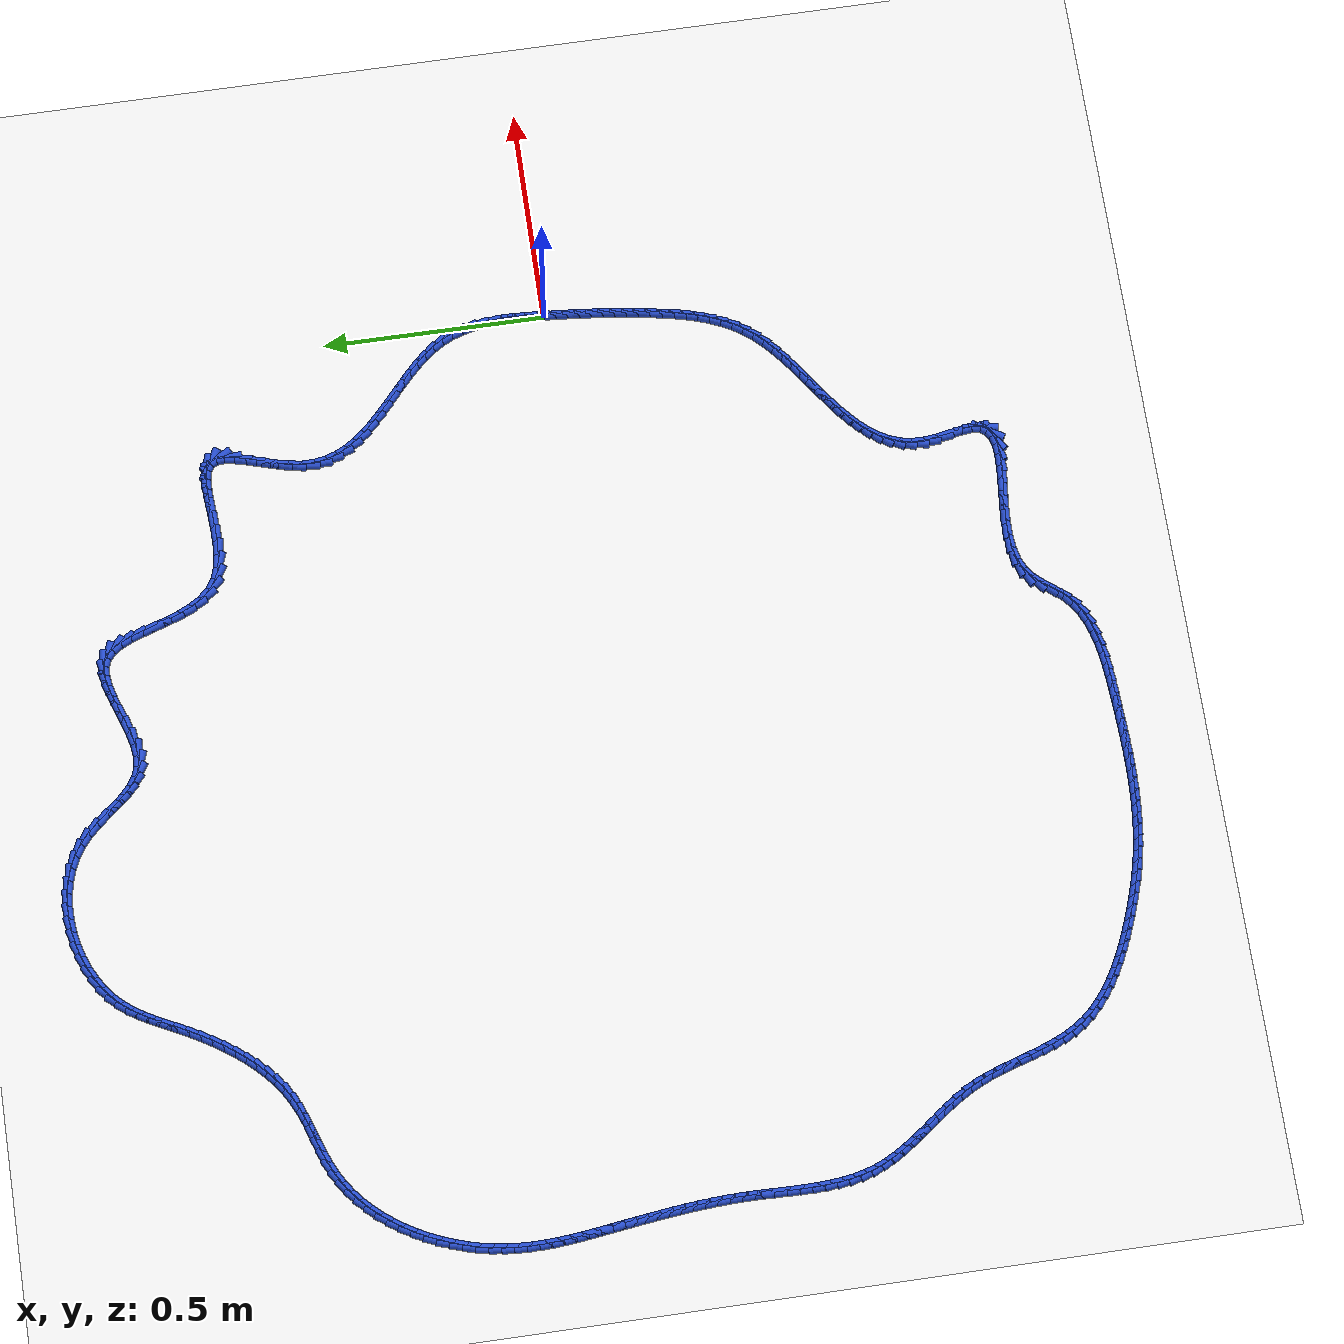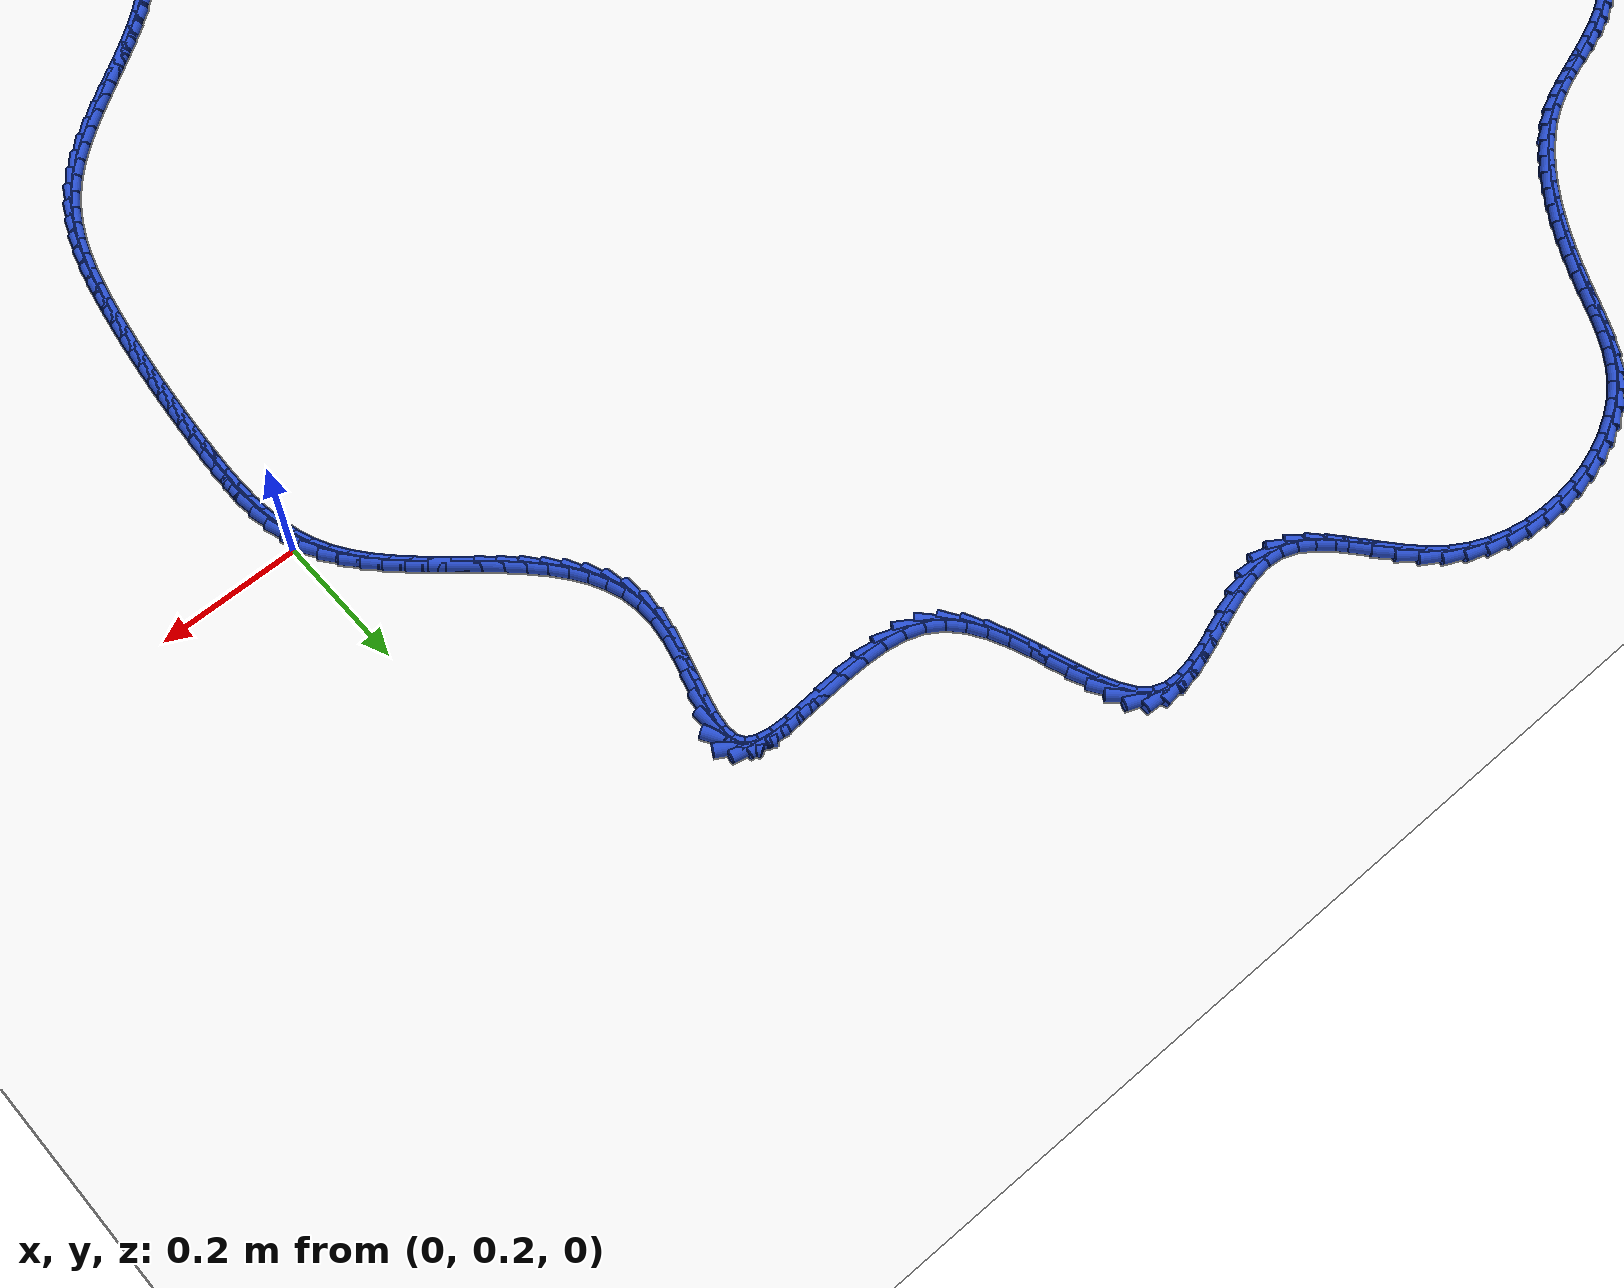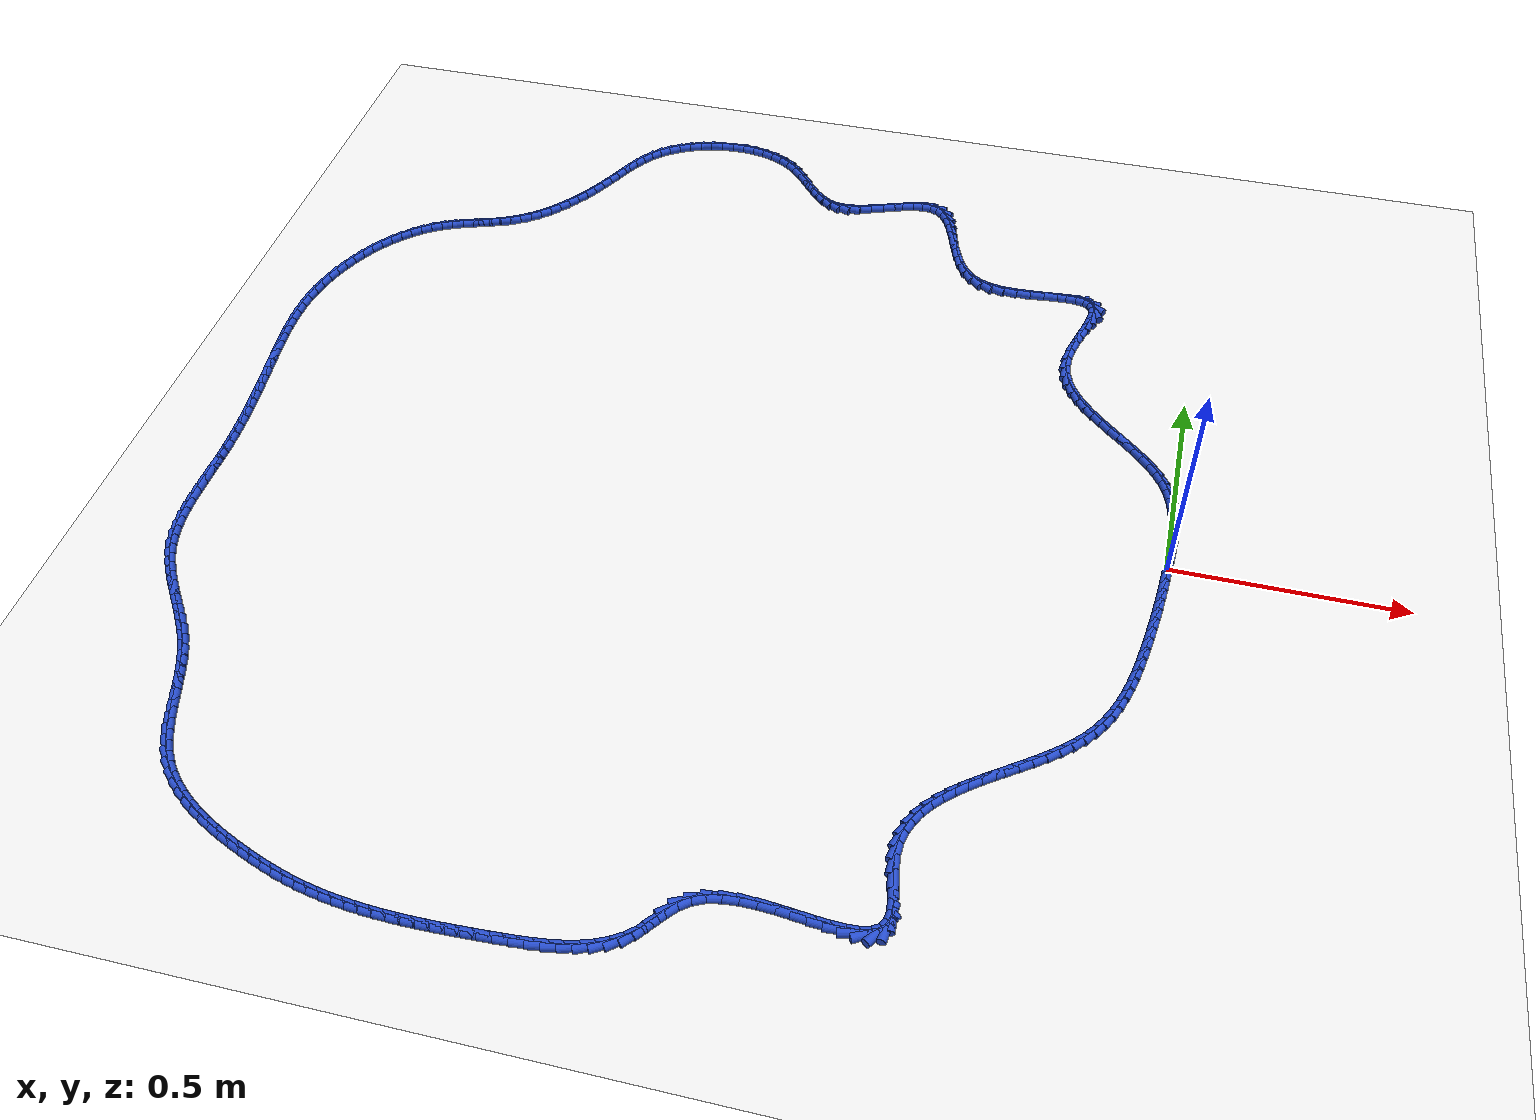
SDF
<sdf version="1.6">
 <world name="default">
  <light name="sun" type="directional">
   <pose>0 0 10 0 -0 0</pose>
   <diffuse>0.8 0.8 0.8 1</diffuse>
   <specular>0.2 0.2 0.2 1</specular>
   <attenuation>
    <range>1000</range>
    <constant>0.9</constant>
    <linear>0.01</linear>
    <quadratic>0.001</quadratic>
   </attenuation>
   <direction>-0.5 0.1 -0.9</direction>
  </light>
  <model name="ground_plane">
   <static>1</static>
   <link name="link">
    <collision name="collision">
     <geometry><plane><normal>0 0 1</normal><size>100 100</size></plane></geometry>
     <surface><friction><ode><mu>100</mu><mu2>50</mu2></ode></friction></surface>
    </collision>
    <visual name="visual">
     <cast_shadows>0</cast_shadows>
     <geometry><plane><normal>0 0 1</normal><size>100 100</size></plane></geometry>
     <material>
      <script><uri>file://media/materials/scripts/gazebo.material</uri><name>Gazebo/WhiteGlow</name></script>
     </material>
    </visual>
   </link>
  </model>
  <gravity>0 0 -9.8</gravity>
  <magnetic_field>6e-06 2.3e-05 -4.2e-05</magnetic_field>
  <atmosphere type="adiabatic"/>
  <physics name="default_physics" default="0" type="ode">
   <max_step_size>0.001</max_step_size>
   <real_time_factor>1</real_time_factor>
   <real_time_update_rate>1000</real_time_update_rate>
  </physics>
  <scene><ambient>0.4 0.4 0.4 1</ambient><background>0.7 0.7 0.7 1</background><shadows>1</shadows></scene>
  <spherical_coordinates>
   <surface_model>EARTH_WGS84</surface_model>
   <latitude_deg>0</latitude_deg>
   <longitude_deg>0</longitude_deg>
   <elevation>0</elevation>
   <heading_deg>0</heading_deg>
  </spherical_coordinates>
  <model name="line">
   <link name="link_0">
    <pose>6.071532165918825e-18 3.469446951953614e-17 0.01 0 1.57 1.5069096707676282</pose>
    <collision name="collision">
     <geometry><cylinder><radius>0.01</radius><length>0.08</length></cylinder></geometry>
    </collision>
    <visual name="visual">
     <material>
      <script><name>Gazebo/Blue</name><uri>file://media/materials/scripts/gazebo.material</uri></script>
     </material>
     <geometry><cylinder><radius>0.01</radius><length>0.08</length></cylinder></geometry>
    </visual>
   </link>
   <link name="link_1">
    <pose>0.0017580394626447399 0.02748065253745607 0.01 0 1.57 1.5268968119250108</pose>
    <collision name="collision">
     <geometry><cylinder><radius>0.01</radius><length>0.08</length></cylinder></geometry>
    </collision>
    <visual name="visual">
     <material>
      <script><name>Gazebo/Blue</name><uri>file://media/materials/scripts/gazebo.material</uri></script>
     </material>
     <geometry><cylinder><radius>0.01</radius><length>0.08</length></cylinder></geometry>
    </visual>
   </link>
   <link name="link_2">
    <pose>0.00297305319521827 0.055140027003314086 0.01 0 1.57 1.5581401452712988</pose>
    <collision name="collision">
     <geometry><cylinder><radius>0.01</radius><length>0.08</length></cylinder></geometry>
    </collision>
    <visual name="visual">
     <material>
      <script><name>Gazebo/Blue</name><uri>file://media/materials/scripts/gazebo.material</uri></script>
     </material>
     <geometry><cylinder><radius>0.01</radius><length>0.08</length></cylinder></geometry>
    </visual>
   </link>
   <link name="link_3">
    <pose>0.0033229610822005785 0.08278574332831226 0.01 0 1.57 -1.5402923842408789</pose>
    <collision name="collision">
     <geometry><cylinder><radius>0.01</radius><length>0.08</length></cylinder></geometry>
    </collision>
    <visual name="visual">
     <material>
      <script><name>Gazebo/Blue</name><uri>file://media/materials/scripts/gazebo.material</uri></script>
     </material>
     <geometry><cylinder><radius>0.01</radius><length>0.08</length></cylinder></geometry>
    </visual>
   </link>
   <link name="link_4">
    <pose>0.0024856830080716495 0.11022542144318874 0.01 0 1.57 -1.4842367252459752</pose>
    <collision name="collision">
     <geometry><cylinder><radius>0.01</radius><length>0.08</length></cylinder></geometry>
    </collision>
    <visual name="visual">
     <material>
      <script><name>Gazebo/Blue</name><uri>file://media/materials/scripts/gazebo.material</uri></script>
     </material>
     <geometry><cylinder><radius>0.01</radius><length>0.08</length></cylinder></geometry>
    </visual>
   </link>
   <link name="link_5">
    <pose>0.00013913885731146967 0.13726668127868177 0.01 0 1.57 -1.4141390577073683</pose>
    <collision name="collision">
     <geometry><cylinder><radius>0.01</radius><length>0.08</length></cylinder></geometry>
    </collision>
    <visual name="visual">
     <material>
      <script><name>Gazebo/Blue</name><uri>file://media/materials/scripts/gazebo.material</uri></script>
     </material>
     <geometry><cylinder><radius>0.01</radius><length>0.08</length></cylinder></geometry>
    </visual>
   </link>
   <link name="link_6">
    <pose>-0.004038751485599986 0.16371714276552943 0.01 0 1.57 -1.328955406196113</pose>
    <collision name="collision">
     <geometry><cylinder><radius>0.01</radius><length>0.08</length></cylinder></geometry>
    </collision>
    <visual name="visual">
     <material>
      <script><name>Gazebo/Blue</name><uri>file://media/materials/scripts/gazebo.material</uri></script>
     </material>
     <geometry><cylinder><radius>0.01</radius><length>0.08</length></cylinder></geometry>
    </visual>
   </link>
   <link name="link_7">
    <pose>-0.010370068136182723 0.18938442583447004 0.01 0 1.57 -1.228190893494446</pose>
    <collision name="collision">
     <geometry><cylinder><radius>0.01</radius><length>0.08</length></cylinder></geometry>
    </collision>
    <visual name="visual">
     <material>
      <script><name>Gazebo/Blue</name><uri>file://media/materials/scripts/gazebo.material</uri></script>
     </material>
     <geometry><cylinder><radius>0.01</radius><length>0.08</length></cylinder></geometry>
    </visual>
   </link>
   <link name="link_8">
    <pose>-0.01917689120995676 0.2140761504162416 0.01 0 1.57 -1.1126762332230302</pose>
    <collision name="collision">
     <geometry><cylinder><radius>0.01</radius><length>0.08</length></cylinder></geometry>
    </collision>
    <visual name="visual">
     <material>
      <script><name>Gazebo/Blue</name><uri>file://media/materials/scripts/gazebo.material</uri></script>
     </material>
     <geometry><cylinder><radius>0.01</radius><length>0.08</length></cylinder></geometry>
    </visual>
   </link>
   <link name="link_9">
    <pose>-0.030777596258192232 0.23760176326670743 0.01 0 1.57 -0.9965495215671685</pose>
    <collision name="collision">
     <geometry><cylinder><radius>0.01</radius><length>0.08</length></cylinder></geometry>
    </collision>
    <visual name="visual">
     <material>
      <script><name>Gazebo/Blue</name><uri>file://media/materials/scripts/gazebo.material</uri></script>
     </material>
     <geometry><cylinder><radius>0.01</radius><length>0.08</length></cylinder></geometry>
    </visual>
   </link>
   <link name="link_10">
    <pose>-0.04520992030766205 0.2599091019140395 0.01 0 1.57 -0.9014258694540425</pose>
    <collision name="collision">
     <geometry><cylinder><radius>0.01</radius><length>0.08</length></cylinder></geometry>
    </collision>
    <visual name="visual">
     <material>
      <script><name>Gazebo/Blue</name><uri>file://media/materials/scripts/gazebo.material</uri></script>
     </material>
     <geometry><cylinder><radius>0.01</radius><length>0.08</length></cylinder></geometry>
    </visual>
   </link>
   <link name="link_11">
    <pose>-0.0620392492085431 0.28117893357504437 0.01 0 1.57 -0.8284798677416844</pose>
    <collision name="collision">
     <geometry><cylinder><radius>0.01</radius><length>0.08</length></cylinder></geometry>
    </collision>
    <visual name="visual">
     <material>
      <script><name>Gazebo/Blue</name><uri>file://media/materials/scripts/gazebo.material</uri></script>
     </material>
     <geometry><cylinder><radius>0.01</radius><length>0.08</length></cylinder></geometry>
    </visual>
   </link>
   <link name="link_12">
    <pose>-0.08078563250280894 0.30161438207888996 0.01 0 1.57 -0.7759130741640365</pose>
    <collision name="collision">
     <geometry><cylinder><radius>0.01</radius><length>0.08</length></cylinder></geometry>
    </collision>
    <visual name="visual">
     <material>
      <script><name>Gazebo/Blue</name><uri>file://media/materials/scripts/gazebo.material</uri></script>
     </material>
     <geometry><cylinder><radius>0.01</radius><length>0.08</length></cylinder></geometry>
    </visual>
   </link>
   <link name="link_13">
    <pose>-0.10096911973243322 0.3214185712547443 0.01 0 1.57 -0.7418735707848516</pose>
    <collision name="collision">
     <geometry><cylinder><radius>0.01</radius><length>0.08</length></cylinder></geometry>
    </collision>
    <visual name="visual">
     <material>
      <script><name>Gazebo/Blue</name><uri>file://media/materials/scripts/gazebo.material</uri></script>
     </material>
     <geometry><cylinder><radius>0.01</radius><length>0.08</length></cylinder></geometry>
    </visual>
   </link>
   <link name="link_14">
    <pose>-0.12210976043938972 0.34079462493177565 0.01 0 1.57 -0.7249648728377506</pose>
    <collision name="collision">
     <geometry><cylinder><radius>0.01</radius><length>0.08</length></cylinder></geometry>
    </collision>
    <visual name="visual">
     <material>
      <script><name>Gazebo/Blue</name><uri>file://media/materials/scripts/gazebo.material</uri></script>
     </material>
     <geometry><cylinder><radius>0.01</radius><length>0.08</length></cylinder></geometry>
    </visual>
   </link>
   <link name="link_15">
    <pose>-0.14372760416565195 0.35994566693915175 0.01 0 1.57 -0.7244603814829383</pose>
    <collision name="collision">
     <geometry><cylinder><radius>0.01</radius><length>0.08</length></cylinder></geometry>
    </collision>
    <visual name="visual">
     <material>
      <script><name>Gazebo/Blue</name><uri>file://media/materials/scripts/gazebo.material</uri></script>
     </material>
     <geometry><cylinder><radius>0.01</radius><length>0.08</length></cylinder></geometry>
    </visual>
   </link>
   <link name="link_16">
    <pose>-0.1653427004531936 0.37907482110604085 0.01 0 1.57 -0.740377107047922</pose>
    <collision name="collision">
     <geometry><cylinder><radius>0.01</radius><length>0.08</length></cylinder></geometry>
    </collision>
    <visual name="visual">
     <material>
      <script><name>Gazebo/Blue</name><uri>file://media/materials/scripts/gazebo.material</uri></script>
     </material>
     <geometry><cylinder><radius>0.01</radius><length>0.08</length></cylinder></geometry>
    </visual>
   </link>
   <link name="link_17">
    <pose>-0.18647509884398833 0.3983852112616108 0.01 0 1.57 -0.7734833623869911</pose>
    <collision name="collision">
     <geometry><cylinder><radius>0.01</radius><length>0.08</length></cylinder></geometry>
    </collision>
    <visual name="visual">
     <material>
      <script><name>Gazebo/Blue</name><uri>file://media/materials/scripts/gazebo.material</uri></script>
     </material>
     <geometry><cylinder><radius>0.01</radius><length>0.08</length></cylinder></geometry>
    </visual>
   </link>
   <link name="link_18">
    <pose>-0.20664484888000972 0.4180799612350295 0.01 0 1.57 -0.8252413813281131</pose>
    <collision name="collision">
     <geometry><cylinder><radius>0.01</radius><length>0.08</length></cylinder></geometry>
    </collision>
    <visual name="visual">
     <material>
      <script><name>Gazebo/Blue</name><uri>file://media/materials/scripts/gazebo.material</uri></script>
     </material>
     <geometry><cylinder><radius>0.01</radius><length>0.08</length></cylinder></geometry>
    </visual>
   </link>
   <link name="link_19">
    <pose>-0.2253720001032316 0.43836219485546546 0.01 0 1.57 -0.8976103176153315</pose>
    <collision name="collision">
     <geometry><cylinder><radius>0.01</radius><length>0.08</length></cylinder></geometry>
    </collision>
    <visual name="visual">
     <material>
      <script><name>Gazebo/Blue</name><uri>file://media/materials/scripts/gazebo.material</uri></script>
     </material>
     <geometry><cylinder><radius>0.01</radius><length>0.08</length></cylinder></geometry>
    </visual>
   </link>
   <link name="link_20">
    <pose>-0.24217660205562738 0.4594350359520862 0.01 0 1.57 -0.992549201913956</pose>
    <collision name="collision">
     <geometry><cylinder><radius>0.01</radius><length>0.08</length></cylinder></geometry>
    </collision>
    <visual name="visual">
     <material>
      <script><name>Gazebo/Blue</name><uri>file://media/materials/scripts/gazebo.material</uri></script>
     </material>
     <geometry><cylinder><radius>0.01</radius><length>0.08</length></cylinder></geometry>
    </visual>
   </link>
   <link name="link_21">
    <pose>-0.2565787042791709 0.4815016083540599 0.01 0 1.57 -1.1110098002361324</pose>
    <collision name="collision">
     <geometry><cylinder><radius>0.01</radius><length>0.08</length></cylinder></geometry>
    </collision>
    <visual name="visual">
     <material>
      <script><name>Gazebo/Blue</name><uri>file://media/materials/scripts/gazebo.material</uri></script>
     </material>
     <geometry><cylinder><radius>0.01</radius><length>0.08</length></cylinder></geometry>
    </visual>
   </link>
   <link name="link_22">
    <pose>-0.26809835631583573 0.5047650358905547 0.01 0 1.57 -1.2513787958632676</pose>
    <collision name="collision">
     <geometry><cylinder><radius>0.01</radius><length>0.08</length></cylinder></geometry>
    </collision>
    <visual name="visual">
     <material>
      <script><name>Gazebo/Blue</name><uri>file://media/materials/scripts/gazebo.material</uri></script>
     </material>
     <geometry><cylinder><radius>0.01</radius><length>0.08</length></cylinder></geometry>
    </visual>
   </link>
   <link name="link_23">
    <pose>-0.27625560770759555 0.5294284423907386 0.01 0 1.57 -1.4079767066610775</pose>
    <collision name="collision">
     <geometry><cylinder><radius>0.01</radius><length>0.08</length></cylinder></geometry>
    </collision>
    <visual name="visual">
     <material>
      <script><name>Gazebo/Blue</name><uri>file://media/materials/scripts/gazebo.material</uri></script>
     </material>
     <geometry><cylinder><radius>0.01</radius><length>0.08</length></cylinder></geometry>
    </visual>
   </link>
   <link name="link_24">
    <pose>-0.28057050799642397 0.5556949516837795 0.01 0 1.57 1.5705443147911478</pose>
    <collision name="collision">
     <geometry><cylinder><radius>0.01</radius><length>0.08</length></cylinder></geometry>
    </collision>
    <visual name="visual">
     <material>
      <script><name>Gazebo/Blue</name><uri>file://media/materials/scripts/gazebo.material</uri></script>
     </material>
     <geometry><cylinder><radius>0.01</radius><length>0.08</length></cylinder></geometry>
    </visual>
   </link>
   <link name="link_25">
    <pose>-0.2805634333794303 0.5837674908432817 0.01 0 1.57 1.4257920130230182</pose>
    <collision name="collision">
     <geometry><cylinder><radius>0.01</radius><length>0.08</length></cylinder></geometry>
    </collision>
    <visual name="visual">
     <material>
      <script><name>Gazebo/Blue</name><uri>file://media/materials/scripts/gazebo.material</uri></script>
     </material>
     <geometry><cylinder><radius>0.01</radius><length>0.08</length></cylinder></geometry>
    </visual>
   </link>
   <link name="link_26">
    <pose>-0.2762107650227242 0.6135743195492026 0.01 0 1.57 1.335130860862073</pose>
    <collision name="collision">
     <geometry><cylinder><radius>0.01</radius><length>0.08</length></cylinder></geometry>
    </collision>
    <visual name="visual">
     <material>
      <script><name>Gazebo/Blue</name><uri>file://media/materials/scripts/gazebo.material</uri></script>
     </material>
     <geometry><cylinder><radius>0.01</radius><length>0.08</length></cylinder></geometry>
    </visual>
   </link>
   <link name="link_27">
    <pose>-0.268851136227735 0.6442231664150978 0.01 0 1.57 1.2901959788291775</pose>
    <collision name="collision">
     <geometry><cylinder><radius>0.01</radius><length>0.08</length></cylinder></geometry>
    </collision>
    <visual name="visual">
     <material>
      <script><name>Gazebo/Blue</name><uri>file://media/materials/scripts/gazebo.material</uri></script>
     </material>
     <geometry><cylinder><radius>0.01</radius><length>0.08</length></cylinder></geometry>
    </visual>
   </link>
   <link name="link_28">
    <pose>-0.26007645305476546 0.6746692052068983 0.01 0 1.57 1.2844276344993268</pose>
    <collision name="collision">
     <geometry><cylinder><radius>0.01</radius><length>0.08</length></cylinder></geometry>
    </collision>
    <visual name="visual">
     <material>
      <script><name>Gazebo/Blue</name><uri>file://media/materials/scripts/gazebo.material</uri></script>
     </material>
     <geometry><cylinder><radius>0.01</radius><length>0.08</length></cylinder></geometry>
    </visual>
   </link>
   <link name="link_29">
    <pose>-0.2514786215641184 0.7038676096905362 0.01 0 1.57 1.322232350640513</pose>
    <collision name="collision">
     <geometry><cylinder><radius>0.01</radius><length>0.08</length></cylinder></geometry>
    </collision>
    <visual name="visual">
     <material>
      <script><name>Gazebo/Blue</name><uri>file://media/materials/scripts/gazebo.material</uri></script>
     </material>
     <geometry><cylinder><radius>0.01</radius><length>0.08</length></cylinder></geometry>
    </visual>
   </link>
   <link name="link_30">
    <pose>-0.24464954781609638 0.730773553631943 0.01 0 1.57 1.4246831106242652</pose>
    <collision name="collision">
     <geometry><cylinder><radius>0.01</radius><length>0.08</length></cylinder></geometry>
    </collision>
    <visual name="visual">
     <material>
      <script><name>Gazebo/Blue</name><uri>file://media/materials/scripts/gazebo.material</uri></script>
     </material>
     <geometry><cylinder><radius>0.01</radius><length>0.08</length></cylinder></geometry>
    </visual>
   </link>
   <link name="link_31">
    <pose>-0.2411811378710022 0.7543422107970507 0.01 0 1.57 -1.4935958551466102</pose>
    <collision name="collision">
     <geometry><cylinder><radius>0.01</radius><length>0.08</length></cylinder></geometry>
    </collision>
    <visual name="visual">
     <material>
      <script><name>Gazebo/Blue</name><uri>file://media/materials/scripts/gazebo.material</uri></script>
     </material>
     <geometry><cylinder><radius>0.01</radius><length>0.08</length></cylinder></geometry>
    </visual>
   </link>
   <link name="link_32">
    <pose>-0.2426652977891386 0.7735287549517907 0.01 0 1.57 -1.0463394015341139</pose>
    <collision name="collision">
     <geometry><cylinder><radius>0.01</radius><length>0.08</length></cylinder></geometry>
    </collision>
    <visual name="visual">
     <material>
      <script><name>Gazebo/Blue</name><uri>file://media/materials/scripts/gazebo.material</uri></script>
     </material>
     <geometry><cylinder><radius>0.01</radius><length>0.08</length></cylinder></geometry>
    </visual>
   </link>
   <link name="link_33">
    <pose>-0.2506469109383618 0.7873259574337156 0.01 0 1.57 -0.5165842766796802</pose>
    <collision name="collision">
     <geometry><cylinder><radius>0.01</radius><length>0.08</length></cylinder></geometry>
    </collision>
    <visual name="visual">
     <material>
      <script><name>Gazebo/Blue</name><uri>file://media/materials/scripts/gazebo.material</uri></script>
     </material>
     <geometry><cylinder><radius>0.01</radius><length>0.08</length></cylinder></geometry>
    </visual>
   </link>
   <link name="link_34">
    <pose>-0.2654266824783944 0.7957213875567517 0.01 0 1.57 -0.19490272206394027</pose>
    <collision name="collision">
     <geometry><cylinder><radius>0.01</radius><length>0.08</length></cylinder></geometry>
    </collision>
    <visual name="visual">
     <material>
      <script><name>Gazebo/Blue</name><uri>file://media/materials/scripts/gazebo.material</uri></script>
     </material>
     <geometry><cylinder><radius>0.01</radius><length>0.08</length></cylinder></geometry>
    </visual>
   </link>
   <link name="link_35">
    <pose>-0.2859634464700576 0.7997755241625881 0.01 0 1.57 -0.032806854001937114</pose>
    <collision name="collision">
     <geometry><cylinder><radius>0.01</radius><length>0.08</length></cylinder></geometry>
    </collision>
    <visual name="visual">
     <material>
      <script><name>Gazebo/Blue</name><uri>file://media/materials/scripts/gazebo.material</uri></script>
     </material>
     <geometry><cylinder><radius>0.01</radius><length>0.08</length></cylinder></geometry>
    </visual>
   </link>
   <link name="link_36">
    <pose>-0.31114944070004913 0.8006020939623105 0.01 0 1.57 0.044779791011084216</pose>
    <collision name="collision">
     <geometry><cylinder><radius>0.01</radius><length>0.08</length></cylinder></geometry>
    </collision>
    <visual name="visual">
     <material>
      <script><name>Gazebo/Blue</name><uri>file://media/materials/scripts/gazebo.material</uri></script>
     </material>
     <geometry><cylinder><radius>0.01</radius><length>0.08</length></cylinder></geometry>
    </visual>
   </link>
   <link name="link_37">
    <pose>-0.3398769029550665 0.7993148236670048 0.01 0 1.57 0.07327352258030873</pose>
    <collision name="collision">
     <geometry><cylinder><radius>0.01</radius><length>0.08</length></cylinder></geometry>
    </collision>
    <visual name="visual">
     <material>
      <script><name>Gazebo/Blue</name><uri>file://media/materials/scripts/gazebo.material</uri></script>
     </material>
     <geometry><cylinder><radius>0.01</radius><length>0.08</length></cylinder></geometry>
    </visual>
   </link>
   <link name="link_38">
    <pose>-0.37103807102180736 0.797027439987756 0.01 0 1.57 0.06681218499301486</pose>
    <collision name="collision">
     <geometry><cylinder><radius>0.01</radius><length>0.08</length></cylinder></geometry>
    </collision>
    <visual name="visual">
     <material>
      <script><name>Gazebo/Blue</name><uri>file://media/materials/scripts/gazebo.material</uri></script>
     </material>
     <geometry><cylinder><radius>0.01</radius><length>0.08</length></cylinder></geometry>
    </visual>
   </link>
   <link name="link_39">
    <pose>-0.40352518268696896 0.7948536696356499 0.01 0 1.57 0.02893006522902035</pose>
    <collision name="collision">
     <geometry><cylinder><radius>0.01</radius><length>0.08</length></cylinder></geometry>
    </collision>
    <visual name="visual">
     <material>
      <script><name>Gazebo/Blue</name><uri>file://media/materials/scripts/gazebo.material</uri></script>
     </material>
     <geometry><cylinder><radius>0.01</radius><length>0.08</length></cylinder></geometry>
    </visual>
   </link>
   <link name="link_40">
    <pose>-0.4362304757372488 0.793907239321772 0.01 0 1.57 -0.043806789329072726</pose>
    <collision name="collision">
     <geometry><cylinder><radius>0.01</radius><length>0.08</length></cylinder></geometry>
    </collision>
    <visual name="visual">
     <material>
      <script><name>Gazebo/Blue</name><uri>file://media/materials/scripts/gazebo.material</uri></script>
     </material>
     <geometry><cylinder><radius>0.01</radius><length>0.08</length></cylinder></geometry>
    </visual>
   </link>
   <link name="link_41">
    <pose>-0.46804618795934494 0.795301875757208 0.01 0 1.57 -0.16122079600361436</pose>
    <collision name="collision">
     <geometry><cylinder><radius>0.01</radius><length>0.08</length></cylinder></geometry>
    </collision>
    <visual name="visual">
     <material>
      <script><name>Gazebo/Blue</name><uri>file://media/materials/scripts/gazebo.material</uri></script>
     </material>
     <geometry><cylinder><radius>0.01</radius><length>0.08</length></cylinder></geometry>
    </visual>
   </link>
   <link name="link_42">
    <pose>-0.4978645571399546 0.8001513056530433 0.01 0 1.57 -0.3389510142445595</pose>
    <collision name="collision">
     <geometry><cylinder><radius>0.01</radius><length>0.08</length></cylinder></geometry>
    </collision>
    <visual name="visual">
     <material>
      <script><name>Gazebo/Blue</name><uri>file://media/materials/scripts/gazebo.material</uri></script>
     </material>
     <geometry><cylinder><radius>0.01</radius><length>0.08</length></cylinder></geometry>
    </visual>
   </link>
   <link name="link_43">
    <pose>-0.5245778210657752 0.8095692557203633 0.01 0 1.57 -0.5856045023158087</pose>
    <collision name="collision">
     <geometry><cylinder><radius>0.01</radius><length>0.08</length></cylinder></geometry>
    </collision>
    <visual name="visual">
     <material>
      <script><name>Gazebo/Blue</name><uri>file://media/materials/scripts/gazebo.material</uri></script>
     </material>
     <geometry><cylinder><radius>0.01</radius><length>0.08</length></cylinder></geometry>
    </visual>
   </link>
   <link name="link_44">
    <pose>-0.5471715535836019 0.8245536058656516 0.01 0 1.57 -0.8289837653993054</pose>
    <collision name="collision">
     <geometry><cylinder><radius>0.01</radius><length>0.08</length></cylinder></geometry>
    </collision>
    <visual name="visual">
     <material>
      <script><name>Gazebo/Blue</name><uri>file://media/materials/scripts/gazebo.material</uri></script>
     </material>
     <geometry><cylinder><radius>0.01</radius><length>0.08</length></cylinder></geometry>
    </visual>
   </link>
   <link name="link_45">
    <pose>-0.565701671827599 0.8447737478468663 0.01 0 1.57 -1.0112187923751723</pose>
    <collision name="collision">
     <geometry><cylinder><radius>0.01</radius><length>0.08</length></cylinder></geometry>
    </collision>
    <visual name="visual">
     <material>
      <script><name>Gazebo/Blue</name><uri>file://media/materials/scripts/gazebo.material</uri></script>
     </material>
     <geometry><cylinder><radius>0.01</radius><length>0.08</length></cylinder></geometry>
    </visual>
   </link>
   <link name="link_46">
    <pose>-0.5809077257487009 0.869050562382806 0.01 0 1.57 -1.135167761497462</pose>
    <collision name="collision">
     <geometry><cylinder><radius>0.01</radius><length>0.08</length></cylinder></geometry>
    </collision>
    <visual name="visual">
     <material>
      <script><name>Gazebo/Blue</name><uri>file://media/materials/scripts/gazebo.material</uri></script>
     </material>
     <geometry><cylinder><radius>0.01</radius><length>0.08</length></cylinder></geometry>
    </visual>
   </link>
   <link name="link_47">
    <pose>-0.5935403526587888 0.8961911687871325 0.01 0 1.57 -1.2118577550688658</pose>
    <collision name="collision">
     <geometry><cylinder><radius>0.01</radius><length>0.08</length></cylinder></geometry>
    </collision>
    <visual name="visual">
     <material>
      <script><name>Gazebo/Blue</name><uri>file://media/materials/scripts/gazebo.material</uri></script>
     </material>
     <geometry><cylinder><radius>0.01</radius><length>0.08</length></cylinder></geometry>
    </visual>
   </link>
   <link name="link_48">
    <pose>-0.6043501898697429 0.9250026863735061 0.01 0 1.57 -1.2498294674316337</pose>
    <collision name="collision">
     <geometry><cylinder><radius>0.01</radius><length>0.08</length></cylinder></geometry>
    </collision>
    <visual name="visual">
     <material>
      <script><name>Gazebo/Blue</name><uri>file://media/materials/scripts/gazebo.material</uri></script>
     </material>
     <geometry><cylinder><radius>0.01</radius><length>0.08</length></cylinder></geometry>
    </visual>
   </link>
   <link name="link_49">
    <pose>-0.6140878746934438 0.9542922344555878 0.01 0 1.57 -1.252474261627351</pose>
    <collision name="collision">
     <geometry><cylinder><radius>0.01</radius><length>0.08</length></cylinder></geometry>
    </collision>
    <visual name="visual">
     <material>
      <script><name>Gazebo/Blue</name><uri>file://media/materials/scripts/gazebo.material</uri></script>
     </material>
     <geometry><cylinder><radius>0.01</radius><length>0.08</length></cylinder></geometry>
    </visual>
   </link>
   <link name="link_50">
    <pose>-0.6235040444417723 0.9828669323470379 0.01 0 1.57 -1.2171252826905221</pose>
    <collision name="collision">
     <geometry><cylinder><radius>0.01</radius><length>0.08</length></cylinder></geometry>
    </collision>
    <visual name="visual">
     <material>
      <script><name>Gazebo/Blue</name><uri>file://media/materials/scripts/gazebo.material</uri></script>
     </material>
     <geometry><cylinder><radius>0.01</radius><length>0.08</length></cylinder></geometry>
    </visual>
   </link>
   <link name="link_51">
    <pose>-0.633349336426609 1.0095338993615173 0.01 0 1.57 -1.1332141804398486</pose>
    <collision name="collision">
     <geometry><cylinder><radius>0.01</radius><length>0.08</length></cylinder></geometry>
    </collision>
    <visual name="visual">
     <material>
      <script><name>Gazebo/Blue</name><uri>file://media/materials/scripts/gazebo.material</uri></script>
     </material>
     <geometry><cylinder><radius>0.01</radius><length>0.08</length></cylinder></geometry>
    </visual>
   </link>
   <link name="link_52">
    <pose>-0.6443743879598344 1.0331002548126875 0.01 0 1.57 -0.9789645201290234</pose>
    <collision name="collision">
     <geometry><cylinder><radius>0.01</radius><length>0.08</length></cylinder></geometry>
    </collision>
    <visual name="visual">
     <material>
      <script><name>Gazebo/Blue</name><uri>file://media/materials/scripts/gazebo.material</uri></script>
     </material>
     <geometry><cylinder><radius>0.01</radius><length>0.08</length></cylinder></geometry>
    </visual>
   </link>
   <link name="link_53">
    <pose>-0.6573298363533289 1.0523731180142082 0.01 0 1.57 -0.7226050466083892</pose>
    <collision name="collision">
     <geometry><cylinder><radius>0.01</radius><length>0.08</length></cylinder></geometry>
    </collision>
    <visual name="visual">
     <material>
      <script><name>Gazebo/Blue</name><uri>file://media/materials/scripts/gazebo.material</uri></script>
     </material>
     <geometry><cylinder><radius>0.01</radius><length>0.08</length></cylinder></geometry>
    </visual>
   </link>
   <link name="link_54">
    <pose>-0.6729663189189735 1.066159608279741 0.01 0 1.57 -0.3620372644582955</pose>
    <collision name="collision">
     <geometry><cylinder><radius>0.01</radius><length>0.08</length></cylinder></geometry>
    </collision>
    <visual name="visual">
     <material>
      <script><name>Gazebo/Blue</name><uri>file://media/materials/scripts/gazebo.material</uri></script>
     </material>
     <geometry><cylinder><radius>0.01</radius><length>0.08</length></cylinder></geometry>
    </visual>
   </link>
   <link name="link_55">
    <pose>-0.6919831246350965 1.0733618534171836 0.01 0 1.57 -0.04179433932981418</pose>
    <collision name="collision">
     <geometry><cylinder><radius>0.01</radius><length>0.08</length></cylinder></geometry>
    </collision>
    <visual name="visual">
     <material>
      <script><name>Gazebo/Blue</name><uri>file://media/materials/scripts/gazebo.material</uri></script>
     </material>
     <geometry><cylinder><radius>0.01</radius><length>0.08</length></cylinder></geometry>
    </visual>
   </link>
   <link name="link_56">
    <pose>-0.7143154498733547 1.0742957620330702 0.01 0 1.57 0.15610548657679899</pose>
    <collision name="collision">
     <geometry><cylinder><radius>0.01</radius><length>0.08</length></cylinder></geometry>
    </collision>
    <visual name="visual">
     <material>
      <script><name>Gazebo/Blue</name><uri>file://media/materials/scripts/gazebo.material</uri></script>
     </material>
     <geometry><cylinder><radius>0.01</radius><length>0.08</length></cylinder></geometry>
    </visual>
   </link>
   <link name="link_57">
    <pose>-0.7393124472580768 1.0703615843306191 0.01 0 1.57 0.26666022437491976</pose>
    <collision name="collision">
     <geometry><cylinder><radius>0.01</radius><length>0.08</length></cylinder></geometry>
    </collision>
    <visual name="visual">
     <material>
      <script><name>Gazebo/Blue</name><uri>file://media/materials/scripts/gazebo.material</uri></script>
     </material>
     <geometry><cylinder><radius>0.01</radius><length>0.08</length></cylinder></geometry>
    </visual>
   </link>
   <link name="link_58">
    <pose>-0.7663083183560692 1.062987234068303 0.01 0 1.57 0.3199585354639432</pose>
    <collision name="collision">
     <geometry><cylinder><radius>0.01</radius><length>0.08</length></cylinder></geometry>
    </collision>
    <visual name="visual">
     <material>
      <script><name>Gazebo/Blue</name><uri>file://media/materials/scripts/gazebo.material</uri></script>
     </material>
     <geometry><cylinder><radius>0.01</radius><length>0.08</length></cylinder></geometry>
    </visual>
   </link>
   <link name="link_59">
    <pose>-0.794637264734138 1.053600625004596 0.01 0 1.57 0.3312040954945419</pose>
    <collision name="collision">
     <geometry><cylinder><radius>0.01</radius><length>0.08</length></cylinder></geometry>
    </collision>
    <visual name="visual">
     <material>
      <script><name>Gazebo/Blue</name><uri>file://media/materials/scripts/gazebo.material</uri></script>
     </material>
     <geometry><cylinder><radius>0.01</radius><length>0.08</length></cylinder></geometry>
    </visual>
   </link>
   <link name="link_60">
    <pose>-0.8236334879590894 1.0436296708979704 0.01 0 1.57 0.3049446334142017</pose>
    <collision name="collision">
     <geometry><cylinder><radius>0.01</radius><length>0.08</length></cylinder></geometry>
    </collision>
    <visual name="visual">
     <material>
      <script><name>Gazebo/Blue</name><uri>file://media/materials/scripts/gazebo.material</uri></script>
     </material>
     <geometry><cylinder><radius>0.01</radius><length>0.08</length></cylinder></geometry>
    </visual>
   </link>
   <link name="link_61">
    <pose>-0.8526311895977294 1.0345022855068997 0.01 0 1.57 0.23740934042930026</pose>
    <collision name="collision">
     <geometry><cylinder><radius>0.01</radius><length>0.08</length></cylinder></geometry>
    </collision>
    <visual name="visual">
     <material>
      <script><name>Gazebo/Blue</name><uri>file://media/materials/scripts/gazebo.material</uri></script>
     </material>
     <geometry><cylinder><radius>0.01</radius><length>0.08</length></cylinder></geometry>
    </visual>
   </link>
   <link name="link_62">
    <pose>-0.8809645712168644 1.0276463825898572 0.01 0 1.57 0.11636543546562135</pose>
    <collision name="collision">
     <geometry><cylinder><radius>0.01</radius><length>0.08</length></cylinder></geometry>
    </collision>
    <visual name="visual">
     <material>
      <script><name>Gazebo/Blue</name><uri>file://media/materials/scripts/gazebo.material</uri></script>
     </material>
     <geometry><cylinder><radius>0.01</radius><length>0.08</length></cylinder></geometry>
    </visual>
   </link>
   <link name="link_63">
    <pose>-0.9079678343833006 1.024489875905316 0.01 0 1.57 -0.07864642244492971</pose>
    <collision name="collision">
     <geometry><cylinder><radius>0.01</radius><length>0.08</length></cylinder></geometry>
    </collision>
    <visual name="visual">
     <material>
      <script><name>Gazebo/Blue</name><uri>file://media/materials/scripts/gazebo.material</uri></script>
     </material>
     <geometry><cylinder><radius>0.01</radius><length>0.08</length></cylinder></geometry>
    </visual>
   </link>
   <link name="link_64">
    <pose>-0.9329751806638442 1.0264606792117494 0.01 0 1.57 -0.3468033629509957</pose>
    <collision name="collision">
     <geometry><cylinder><radius>0.01</radius><length>0.08</length></cylinder></geometry>
    </collision>
    <visual name="visual">
     <material>
      <script><name>Gazebo/Blue</name><uri>file://media/materials/scripts/gazebo.material</uri></script>
     </material>
     <geometry><cylinder><radius>0.01</radius><length>0.08</length></cylinder></geometry>
    </visual>
   </link>
   <link name="link_65">
    <pose>-0.9555061436471375 1.0346035974529313 0.01 0 1.57 -0.5847785899089406</pose>
    <collision name="collision">
     <geometry><cylinder><radius>0.01</radius><length>0.08</length></cylinder></geometry>
    </collision>
    <visual name="visual">
     <material>
      <script><name>Gazebo/Blue</name><uri>file://media/materials/scripts/gazebo.material</uri></script>
     </material>
     <geometry><cylinder><radius>0.01</radius><length>0.08</length></cylinder></geometry>
    </visual>
   </link>
   <link name="link_66">
    <pose>-0.9759601546480697 1.048144556289821 0.01 0 1.57 -0.7469137109383022</pose>
    <collision name="collision">
     <geometry><cylinder><radius>0.01</radius><length>0.08</length></cylinder></geometry>
    </collision>
    <visual name="visual">
     <material>
      <script><name>Gazebo/Blue</name><uri>file://media/materials/scripts/gazebo.material</uri></script>
     </material>
     <geometry><cylinder><radius>0.01</radius><length>0.08</length></cylinder></geometry>
    </visual>
   </link>
   <link name="link_67">
    <pose>-0.9949975025239539 1.0657702501005542 0.01 0 1.57 -0.8400523257673191</pose>
    <collision name="collision">
     <geometry><cylinder><radius>0.01</radius><length>0.08</length></cylinder></geometry>
    </collision>
    <visual name="visual">
     <material>
      <script><name>Gazebo/Blue</name><uri>file://media/materials/scripts/gazebo.material</uri></script>
     </material>
     <geometry><cylinder><radius>0.01</radius><length>0.08</length></cylinder></geometry>
    </visual>
   </link>
   <link name="link_68">
    <pose>-1.013278517093178 1.086167288590641 0.01 0 1.57 -0.8768006497260558</pose>
    <collision name="collision">
     <geometry><cylinder><radius>0.01</radius><length>0.08</length></cylinder></geometry>
    </collision>
    <visual name="visual">
     <material>
      <script><name>Gazebo/Blue</name><uri>file://media/materials/scripts/gazebo.material</uri></script>
     </material>
     <geometry><cylinder><radius>0.01</radius><length>0.08</length></cylinder></geometry>
    </visual>
   </link>
   <link name="link_69">
    <pose>-1.031463528174129 1.1080222814655913 0.01 0 1.57 -0.8649918103429828</pose>
    <collision name="collision">
     <geometry><cylinder><radius>0.01</radius><length>0.08</length></cylinder></geometry>
    </collision>
    <visual name="visual">
     <material>
      <script><name>Gazebo/Blue</name><uri>file://media/materials/scripts/gazebo.material</uri></script>
     </material>
     <geometry><cylinder><radius>0.01</radius><length>0.08</length></cylinder></geometry>
    </visual>
   </link>
   <link name="link_70">
    <pose>-1.0502128655851939 1.130021838430915 0.01 0 1.57 -0.8063911086124225</pose>
    <collision name="collision">
     <geometry><cylinder><radius>0.01</radius><length>0.08</length></cylinder></geometry>
    </collision>
    <visual name="visual">
     <material>
      <script><name>Gazebo/Blue</name><uri>file://media/materials/scripts/gazebo.material</uri></script>
     </material>
     <geometry><cylinder><radius>0.01</radius><length>0.08</length></cylinder></geometry>
    </visual>
   </link>
   <link name="link_71">
    <pose>-1.0701868591447605 1.1508525691921232 0.01 0 1.57 -0.6985569765102941</pose>
    <collision name="collision">
     <geometry><cylinder><radius>0.01</radius><length>0.08</length></cylinder></geometry>
    </collision>
    <visual name="visual">
     <material>
      <script><name>Gazebo/Blue</name><uri>file://media/materials/scripts/gazebo.material</uri></script>
     </material>
     <geometry><cylinder><radius>0.01</radius><length>0.08</length></cylinder></geometry>
    </visual>
   </link>
   <link name="link_72">
    <pose>-1.0920416746841424 1.1692067808503241 0.01 0 1.57 -0.5595140066091934</pose>
    <collision name="collision">
     <geometry><cylinder><radius>0.01</radius><length>0.08</length></cylinder></geometry>
    </collision>
    <visual name="visual">
     <material>
      <script><name>Gazebo/Blue</name><uri>file://media/materials/scripts/gazebo.material</uri></script>
     </material>
     <geometry><cylinder><radius>0.01</radius><length>0.08</length></cylinder></geometry>
    </visual>
   </link>
   <link name="link_73">
    <pose>-1.1160795489195625 1.184261045742481 0.01 0 1.57 -0.4267110209482854</pose>
    <collision name="collision">
     <geometry><cylinder><radius>0.01</radius><length>0.08</length></cylinder></geometry>
    </collision>
    <visual name="visual">
     <material>
      <script><name>Gazebo/Blue</name><uri>file://media/materials/scripts/gazebo.material</uri></script>
     </material>
     <geometry><cylinder><radius>0.01</radius><length>0.08</length></cylinder></geometry>
    </visual>
   </link>
   <link name="link_74">
    <pose>-1.1419840514399409 1.1960384305162701 0.01 0 1.57 -0.3045058960654811</pose>
    <collision name="collision">
     <geometry><cylinder><radius>0.01</radius><length>0.08</length></cylinder></geometry>
    </collision>
    <visual name="visual">
     <material>
      <script><name>Gazebo/Blue</name><uri>file://media/materials/scripts/gazebo.material</uri></script>
     </material>
     <geometry><cylinder><radius>0.01</radius><length>0.08</length></cylinder></geometry>
    </visual>
   </link>
   <link name="link_75">
    <pose>-1.1693764064032102 1.2046473062590226 0.01 0 1.57 -0.19227765522447926</pose>
    <collision name="collision">
     <geometry><cylinder><radius>0.01</radius><length>0.08</length></cylinder></geometry>
    </collision>
    <visual name="visual">
     <material>
      <script><name>Gazebo/Blue</name><uri>file://media/materials/scripts/gazebo.material</uri></script>
     </material>
     <geometry><cylinder><radius>0.01</radius><length>0.08</length></cylinder></geometry>
    </visual>
   </link>
   <link name="link_76">
    <pose>-1.1978778379673056 1.2101960440580701 0.01 0 1.57 -0.0886081852951144</pose>
    <collision name="collision">
     <geometry><cylinder><radius>0.01</radius><length>0.08</length></cylinder></geometry>
    </collision>
    <visual name="visual">
     <material>
      <script><name>Gazebo/Blue</name><uri>file://media/materials/scripts/gazebo.material</uri></script>
     </material>
     <geometry><cylinder><radius>0.01</radius><length>0.08</length></cylinder></geometry>
    </visual>
   </link>
   <link name="link_77">
    <pose>-1.2271095702901607 1.2127930150007447 0.01 0 1.57 0.008329682058506774</pose>
    <collision name="collision">
     <geometry><cylinder><radius>0.01</radius><length>0.08</length></cylinder></geometry>
    </collision>
    <visual name="visual">
     <material>
      <script><name>Gazebo/Blue</name><uri>file://media/materials/scripts/gazebo.material</uri></script>
     </material>
     <geometry><cylinder><radius>0.01</radius><length>0.08</length></cylinder></geometry>
    </visual>
   </link>
   <link name="link_78">
    <pose>-1.256692827529709 1.212546590174377 0.01 0 1.57 0.10053449087895906</pose>
    <collision name="collision">
     <geometry><cylinder><radius>0.01</radius><length>0.08</length></cylinder></geometry>
    </collision>
    <visual name="visual">
     <material>
      <script><name>Gazebo/Blue</name><uri>file://media/materials/scripts/gazebo.material</uri></script>
     </material>
     <geometry><cylinder><radius>0.01</radius><length>0.08</length></cylinder></geometry>
    </visual>
   </link>
   <link name="link_79">
    <pose>-1.2862488338438847 1.2095651406662997 0.01 0 1.57 0.19006562579602831</pose>
    <collision name="collision">
     <geometry><cylinder><radius>0.01</radius><length>0.08</length></cylinder></geometry>
    </collision>
    <visual name="visual">
     <material>
      <script><name>Gazebo/Blue</name><uri>file://media/materials/scripts/gazebo.material</uri></script>
     </material>
     <geometry><cylinder><radius>0.01</radius><length>0.08</length></cylinder></geometry>
    </visual>
   </link>
   <link name="link_80">
    <pose>-1.3153988133906218 1.2039570375638442 0.01 0 1.57 0.27901818270972845</pose>
    <collision name="collision">
     <geometry><cylinder><radius>0.01</radius><length>0.08</length></cylinder></geometry>
    </collision>
    <visual name="visual">
     <material>
      <script><name>Gazebo/Blue</name><uri>file://media/materials/scripts/gazebo.material</uri></script>
     </material>
     <geometry><cylinder><radius>0.01</radius><length>0.08</length></cylinder></geometry>
    </visual>
   </link>
   <link name="link_81">
    <pose>-1.3437639903278542 1.1958306519543416 0.01 0 1.57 0.3695461246600823</pose>
    <collision name="collision">
     <geometry><cylinder><radius>0.01</radius><length>0.08</length></cylinder></geometry>
    </collision>
    <visual name="visual">
     <material>
      <script><name>Gazebo/Blue</name><uri>file://media/materials/scripts/gazebo.material</uri></script>
     </material>
     <geometry><cylinder><radius>0.01</radius><length>0.08</length></cylinder></geometry>
    </visual>
   </link>
   <link name="link_82">
    <pose>-1.3709655888135162 1.1852943549251238 0.01 0 1.57 0.46390371049397566</pose>
    <collision name="collision">
     <geometry><cylinder><radius>0.01</radius><length>0.08</length></cylinder></geometry>
    </collision>
    <visual name="visual">
     <material>
      <script><name>Gazebo/Blue</name><uri>file://media/materials/scripts/gazebo.material</uri></script>
     </material>
     <geometry><cylinder><radius>0.01</radius><length>0.08</length></cylinder></geometry>
    </visual>
   </link>
   <link name="link_83">
    <pose>-1.3966248330055409 1.172456517563522 0.01 0 1.57 0.5644752112436878</pose>
    <collision name="collision">
     <geometry><cylinder><radius>0.01</radius><length>0.08</length></cylinder></geometry>
    </collision>
    <visual name="visual">
     <material>
      <script><name>Gazebo/Blue</name><uri>file://media/materials/scripts/gazebo.material</uri></script>
     </material>
     <geometry><cylinder><radius>0.01</radius><length>0.08</length></cylinder></geometry>
    </visual>
   </link>
   <link name="link_84">
    <pose>-1.4203629470618626 1.1574255109568679 0.01 0 1.57 0.6737514505017903</pose>
    <collision name="collision">
     <geometry><cylinder><radius>0.01</radius><length>0.08</length></cylinder></geometry>
    </collision>
    <visual name="visual">
     <material>
      <script><name>Gazebo/Blue</name><uri>file://media/materials/scripts/gazebo.material</uri></script>
     </material>
     <geometry><cylinder><radius>0.01</radius><length>0.08</length></cylinder></geometry>
    </visual>
   </link>
   <link name="link_85">
    <pose>-1.441801155140416 1.1403097061924938 0.01 0 1.57 0.7930824446731769</pose>
    <collision name="collision">
     <geometry><cylinder><radius>0.01</radius><length>0.08</length></cylinder></geometry>
    </collision>
    <visual name="visual">
     <material>
      <script><name>Gazebo/Blue</name><uri>file://media/materials/scripts/gazebo.material</uri></script>
     </material>
     <geometry><cylinder><radius>0.01</radius><length>0.08</length></cylinder></geometry>
    </visual>
   </link>
   <link name="link_86">
    <pose>-1.46059423876551 1.1212255575315921 0.01 0 1.57 0.9056455806511068</pose>
    <collision name="collision">
     <geometry><cylinder><radius>0.01</radius><length>0.08</length></cylinder></geometry>
    </collision>
    <visual name="visual">
     <material>
      <script><name>Gazebo/Blue</name><uri>file://media/materials/scripts/gazebo.material</uri></script>
     </material>
     <geometry><cylinder><radius>0.01</radius><length>0.08</length></cylinder></geometry>
    </visual>
   </link>
   <link name="link_87">
    <pose>-1.4769178686747995 1.100414989095741 0.01 0 1.57 0.9940038117101611</pose>
    <collision name="collision">
     <geometry><cylinder><radius>0.01</radius><length>0.08</length></cylinder></geometry>
    </collision>
    <visual name="visual">
     <material>
      <script><name>Gazebo/Blue</name><uri>file://media/materials/scripts/gazebo.material</uri></script>
     </material>
     <geometry><cylinder><radius>0.01</radius><length>0.08</length></cylinder></geometry>
    </visual>
   </link>
   <link name="link_88">
    <pose>-1.491358520066373 1.0782188780602113 0.01 0 1.57 1.055669327323574</pose>
    <collision name="collision">
     <geometry><cylinder><radius>0.01</radius><length>0.08</length></cylinder></geometry>
    </collision>
    <visual name="visual">
     <material>
      <script><name>Gazebo/Blue</name><uri>file://media/materials/scripts/gazebo.material</uri></script>
     </material>
     <geometry><cylinder><radius>0.01</radius><length>0.08</length></cylinder></geometry>
    </visual>
   </link>
   <link name="link_89">
    <pose>-1.504513818778972 1.0549807875252073 0.01 0 1.57 1.0906002266453463</pose>
    <collision name="collision">
     <geometry><cylinder><radius>0.01</radius><length>0.08</length></cylinder></geometry>
    </collision>
    <visual name="visual">
     <material>
      <script><name>Gazebo/Blue</name><uri>file://media/materials/scripts/gazebo.material</uri></script>
     </material>
     <geometry><cylinder><radius>0.01</radius><length>0.08</length></cylinder></geometry>
    </visual>
   </link>
   <link name="link_90">
    <pose>-1.516981390651337 1.031044280590934 0.01 0 1.57 1.099544204715864</pose>
    <collision name="collision">
     <geometry><cylinder><radius>0.01</radius><length>0.08</length></cylinder></geometry>
    </collision>
    <visual name="visual">
     <material>
      <script><name>Gazebo/Blue</name><uri>file://media/materials/scripts/gazebo.material</uri></script>
     </material>
     <geometry><cylinder><radius>0.01</radius><length>0.08</length></cylinder></geometry>
    </visual>
   </link>
   <link name="link_91">
    <pose>-1.5293588615222087 1.0067529203575953 0.01 0 1.57 1.0839855255790194</pose>
    <collision name="collision">
     <geometry><cylinder><radius>0.01</radius><length>0.08</length></cylinder></geometry>
    </collision>
    <visual name="visual">
     <material>
      <script><name>Gazebo/Blue</name><uri>file://media/materials/scripts/gazebo.material</uri></script>
     </material>
     <geometry><cylinder><radius>0.01</radius><length>0.08</length></cylinder></geometry>
    </visual>
   </link>
   <link name="link_92">
    <pose>-1.5422250178712786 0.9824449825350228 0.01 0 1.57 1.0552663763679404</pose>
    <collision name="collision">
     <geometry><cylinder><radius>0.01</radius><length>0.08</length></cylinder></geometry>
    </collision>
    <visual name="visual">
     <material>
      <script><name>Gazebo/Blue</name><uri>file://media/materials/scripts/gazebo.material</uri></script>
     </material>
     <geometry><cylinder><radius>0.01</radius><length>0.08</length></cylinder></geometry>
    </visual>
   </link>
   <link name="link_93">
    <pose>-1.5558635466571789 0.9583759212061321 0.01 0 1.57 1.021830143758305</pose>
    <collision name="collision">
     <geometry><cylinder><radius>0.01</radius><length>0.08</length></cylinder></geometry>
    </collision>
    <visual name="visual">
     <material>
      <script><name>Gazebo/Blue</name><uri>file://media/materials/scripts/gazebo.material</uri></script>
     </material>
     <geometry><cylinder><radius>0.01</radius><length>0.08</length></cylinder></geometry>
    </visual>
   </link>
   <link name="link_94">
    <pose>-1.5703240166690704 0.9347354836454479 0.01 0 1.57 0.983506902265941</pose>
    <collision name="collision">
     <geometry><cylinder><radius>0.01</radius><length>0.08</length></cylinder></geometry>
    </collision>
    <visual name="visual">
     <material>
      <script><name>Gazebo/Blue</name><uri>file://media/materials/scripts/gazebo.material</uri></script>
     </material>
     <geometry><cylinder><radius>0.01</radius><length>0.08</length></cylinder></geometry>
    </visual>
   </link>
   <link name="link_95">
    <pose>-1.585649558846788 0.9117116103026196 0.01 0 1.57 0.9398192109483645</pose>
    <collision name="collision">
     <geometry><cylinder><radius>0.01</radius><length>0.08</length></cylinder></geometry>
    </collision>
    <visual name="visual">
     <material>
      <script><name>Gazebo/Blue</name><uri>file://media/materials/scripts/gazebo.material</uri></script>
     </material>
     <geometry><cylinder><radius>0.01</radius><length>0.08</length></cylinder></geometry>
    </visual>
   </link>
   <link name="link_96">
    <pose>-1.601883304130166 0.8894922416272976 0.01 0 1.57 0.8902358489001854</pose>
    <collision name="collision">
     <geometry><cylinder><radius>0.01</radius><length>0.08</length></cylinder></geometry>
    </collision>
    <visual name="visual">
     <material>
      <script><name>Gazebo/Blue</name><uri>file://media/materials/scripts/gazebo.material</uri></script>
     </material>
     <geometry><cylinder><radius>0.01</radius><length>0.08</length></cylinder></geometry>
    </visual>
   </link>
   <link name="link_97">
    <pose>-1.6190683834590407 0.8682653180691318 0.01 0 1.57 0.8342002158210859</pose>
    <collision name="collision">
     <geometry><cylinder><radius>0.01</radius><length>0.08</length></cylinder></geometry>
    </collision>
    <visual name="visual">
     <material>
      <script><name>Gazebo/Blue</name><uri>file://media/materials/scripts/gazebo.material</uri></script>
     </material>
     <geometry><cylinder><radius>0.01</radius><length>0.08</length></cylinder></geometry>
    </visual>
   </link>
   <link name="link_98">
    <pose>-1.6372479277732468 0.8482187800777728 0.01 0 1.57 0.771177634902061</pose>
    <collision name="collision">
     <geometry><cylinder><radius>0.01</radius><length>0.08</length></cylinder></geometry>
    </collision>
    <visual name="visual">
     <material>
      <script><name>Gazebo/Blue</name><uri>file://media/materials/scripts/gazebo.material</uri></script>
     </material>
     <geometry><cylinder><radius>0.01</radius><length>0.08</length></cylinder></geometry>
    </visual>
   </link>
   <link name="link_99">
    <pose>-1.656465068012619 0.8295405681028705 0.01 0 1.57 0.7007283488129636</pose>
    <collision name="collision">
     <geometry><cylinder><radius>0.01</radius><length>0.08</length></cylinder></geometry>
    </collision>
    <visual name="visual">
     <material>
      <script><name>Gazebo/Blue</name><uri>file://media/materials/scripts/gazebo.material</uri></script>
     </material>
     <geometry><cylinder><radius>0.01</radius><length>0.08</length></cylinder></geometry>
    </visual>
   </link>
   <link name="link_100">
    <pose>-1.6767629351169928 0.812418622594075 0.01 0 1.57 0.6226103694188753</pose>
    <collision name="collision">
     <geometry><cylinder><radius>0.01</radius><length>0.08</length></cylinder></geometry>
    </collision>
    <visual name="visual">
     <material>
      <script><name>Gazebo/Blue</name><uri>file://media/materials/scripts/gazebo.material</uri></script>
     </material>
     <geometry><cylinder><radius>0.01</radius><length>0.08</length></cylinder></geometry>
    </visual>
   </link>
   <link name="link_101">
    <pose>-1.6981846600262038 0.7970408840010367 0.01 0 1.57 0.5369084002489682</pose>
    <collision name="collision">
     <geometry><cylinder><radius>0.01</radius><length>0.08</length></cylinder></geometry>
    </collision>
    <visual name="visual">
     <material>
      <script><name>Gazebo/Blue</name><uri>file://media/materials/scripts/gazebo.material</uri></script>
     </material>
     <geometry><cylinder><radius>0.01</radius><length>0.08</length></cylinder></geometry>
    </visual>
   </link>
   <link name="link_102">
    <pose>-1.7207733736800863 0.7835952927734058 0.01 0 1.57 0.4475327010091419</pose>
    <collision name="collision">
     <geometry><cylinder><radius>0.01</radius><length>0.08</length></cylinder></geometry>
    </collision>
    <visual name="visual">
     <material>
      <script><name>Gazebo/Blue</name><uri>file://media/materials/scripts/gazebo.material</uri></script>
     </material>
     <geometry><cylinder><radius>0.01</radius><length>0.08</length></cylinder></geometry>
    </visual>
   </link>
   <link name="link_103">
    <pose>-1.744534693752783 0.7721894870841439 0.01 0 1.57 0.3774363834782706</pose>
    <collision name="collision">
     <geometry><cylinder><radius>0.01</radius><length>0.08</length></cylinder></geometry>
    </collision>
    <visual name="visual">
     <material>
      <script><name>Gazebo/Blue</name><uri>file://media/materials/scripts/gazebo.material</uri></script>
     </material>
     <geometry><cylinder><radius>0.01</radius><length>0.08</length></cylinder></geometry>
    </visual>
   </link>
   <link name="link_104">
    <pose>-1.7692264215977465 0.7624006203727641 0.01 0 1.57 0.33534031547719884</pose>
    <collision name="collision">
     <geometry><cylinder><radius>0.01</radius><length>0.08</length></cylinder></geometry>
    </collision>
    <visual name="visual">
     <material>
      <script><name>Gazebo/Blue</name><uri>file://media/materials/scripts/gazebo.material</uri></script>
     </material>
     <geometry><cylinder><radius>0.01</radius><length>0.08</length></cylinder></geometry>
    </visual>
   </link>
   <link name="link_105">
    <pose>-1.794505840812203 0.7535906740716695 0.01 0 1.57 0.3203967697265908</pose>
    <collision name="collision">
     <geometry><cylinder><radius>0.01</radius><length>0.08</length></cylinder></geometry>
    </collision>
    <visual name="visual">
     <material>
      <script><name>Gazebo/Blue</name><uri>file://media/materials/scripts/gazebo.material</uri></script>
     </material>
     <geometry><cylinder><radius>0.01</radius><length>0.08</length></cylinder></geometry>
    </visual>
   </link>
   <link name="link_106">
    <pose>-1.820029947707964 0.7451210146395257 0.01 0 1.57 0.33207676167432676</pose>
    <collision name="collision">
     <geometry><cylinder><radius>0.01</radius><length>0.08</length></cylinder></geometry>
    </collision>
    <visual name="visual">
     <material>
      <script><name>Gazebo/Blue</name><uri>file://media/materials/scripts/gazebo.material</uri></script>
     </material>
     <geometry><cylinder><radius>0.01</radius><length>0.08</length></cylinder></geometry>
    </visual>
   </link>
   <link name="link_107">
    <pose>-1.8454557385968353 0.736353008534997 0.01 0 1.57 0.37050194751833143</pose>
    <collision name="collision">
     <geometry><cylinder><radius>0.01</radius><length>0.08</length></cylinder></geometry>
    </collision>
    <visual name="visual">
     <material>
      <script><name>Gazebo/Blue</name><uri>file://media/materials/scripts/gazebo.material</uri></script>
     </material>
     <geometry><cylinder><radius>0.01</radius><length>0.08</length></cylinder></geometry>
    </visual>
   </link>
   <link name="link_108">
    <pose>-1.8704402097906268 0.726648022216749 0.01 0 1.57 0.4361921595259842</pose>
    <collision name="collision">
     <geometry><cylinder><radius>0.01</radius><length>0.08</length></cylinder></geometry>
    </collision>
    <visual name="visual">
     <material>
      <script><name>Gazebo/Blue</name><uri>file://media/materials/scripts/gazebo.material</uri></script>
     </material>
     <geometry><cylinder><radius>0.01</radius><length>0.08</length></cylinder></geometry>
    </visual>
   </link>
   <link name="link_109">
    <pose>-1.8946403624448043 0.7153674346797552 0.01 0 1.57 0.5232091866314043</pose>
    <collision name="collision">
     <geometry><cylinder><radius>0.01</radius><length>0.08</length></cylinder></geometry>
    </collision>
    <visual name="visual">
     <material>
      <script><name>Gazebo/Blue</name><uri>file://media/materials/scripts/gazebo.material</uri></script>
     </material>
     <geometry><cylinder><radius>0.01</radius><length>0.08</length></cylinder></geometry>
    </visual>
   </link>
   <link name="link_110">
    <pose>-1.9177718654428537 0.7020244682000765 0.01 0 1.57 0.609925888993529</pose>
    <collision name="collision">
     <geometry><cylinder><radius>0.01</radius><length>0.08</length></cylinder></geometry>
    </collision>
    <visual name="visual">
     <material>
      <script><name>Gazebo/Blue</name><uri>file://media/materials/scripts/gazebo.material</uri></script>
     </material>
     <geometry><cylinder><radius>0.01</radius><length>0.08</length></cylinder></geometry>
    </visual>
   </link>
   <link name="link_111">
    <pose>-1.9397551657680738 0.6866623498727465 0.01 0 1.57 0.6915799363572562</pose>
    <collision name="collision">
     <geometry><cylinder><radius>0.01</radius><length>0.08</length></cylinder></geometry>
    </collision>
    <visual name="visual">
     <material>
      <script><name>Gazebo/Blue</name><uri>file://media/materials/scripts/gazebo.material</uri></script>
     </material>
     <geometry><cylinder><radius>0.01</radius><length>0.08</length></cylinder></geometry>
    </visual>
   </link>
   <link name="link_112">
    <pose>-1.9605553627344265 0.6694398755496798 0.01 0 1.57 0.7683075674658049</pose>
    <collision name="collision">
     <geometry><cylinder><radius>0.01</radius><length>0.08</length></cylinder></geometry>
    </collision>
    <visual name="visual">
     <material>
      <script><name>Gazebo/Blue</name><uri>file://media/materials/scripts/gazebo.material</uri></script>
     </material>
     <geometry><cylinder><radius>0.01</radius><length>0.08</length></cylinder></geometry>
    </visual>
   </link>
   <link name="link_113">
    <pose>-1.9801375556558747 0.6505158410827907 0.01 0 1.57 0.8404385504691751</pose>
    <collision name="collision">
     <geometry><cylinder><radius>0.01</radius><length>0.08</length></cylinder></geometry>
    </collision>
    <visual name="visual">
     <material>
      <script><name>Gazebo/Blue</name><uri>file://media/materials/scripts/gazebo.material</uri></script>
     </material>
     <geometry><cylinder><radius>0.01</radius><length>0.08</length></cylinder></geometry>
    </visual>
   </link>
   <link name="link_114">
    <pose>-1.9984668438463824 0.6300490423239932 0.01 0 1.57 0.9084302336866495</pose>
    <collision name="collision">
     <geometry><cylinder><radius>0.01</radius><length>0.08</length></cylinder></geometry>
    </collision>
    <visual name="visual">
     <material>
      <script><name>Gazebo/Blue</name><uri>file://media/materials/scripts/gazebo.material</uri></script>
     </material>
     <geometry><cylinder><radius>0.01</radius><length>0.08</length></cylinder></geometry>
    </visual>
   </link>
   <link name="link_115">
    <pose>-2.015508326619911 0.6081982751252019 0.01 0 1.57 0.9728159416372564</pose>
    <collision name="collision">
     <geometry><cylinder><radius>0.01</radius><length>0.08</length></cylinder></geometry>
    </collision>
    <visual name="visual">
     <material>
      <script><name>Gazebo/Blue</name><uri>file://media/materials/scripts/gazebo.material</uri></script>
     </material>
     <geometry><cylinder><radius>0.01</radius><length>0.08</length></cylinder></geometry>
    </visual>
   </link>
   <link name="link_116">
    <pose>-2.031227103290425 0.5851223353383309 0.01 0 1.57 1.0341687422427408</pose>
    <collision name="collision">
     <geometry><cylinder><radius>0.01</radius><length>0.08</length></cylinder></geometry>
    </collision>
    <visual name="visual">
     <material>
      <script><name>Gazebo/Blue</name><uri>file://media/materials/scripts/gazebo.material</uri></script>
     </material>
     <geometry><cylinder><radius>0.01</radius><length>0.08</length></cylinder></geometry>
    </visual>
   </link>
   <link name="link_117">
    <pose>-2.045588273171887 0.5609800188152949 0.01 0 1.57 1.09307878672978</pose>
    <collision name="collision">
     <geometry><cylinder><radius>0.01</radius><length>0.08</length></cylinder></geometry>
    </collision>
    <visual name="visual">
     <material>
      <script><name>Gazebo/Blue</name><uri>file://media/materials/scripts/gazebo.material</uri></script>
     </material>
     <geometry><cylinder><radius>0.01</radius><length>0.08</length></cylinder></geometry>
    </visual>
   </link>
   <link name="link_118">
    <pose>-2.0585569355782583 0.5359301214080081 0.01 0 1.57 1.1501414262136973</pose>
    <collision name="collision">
     <geometry><cylinder><radius>0.01</radius><length>0.08</length></cylinder></geometry>
    </collision>
    <visual name="visual">
     <material>
      <script><name>Gazebo/Blue</name><uri>file://media/materials/scripts/gazebo.material</uri></script>
     </material>
     <geometry><cylinder><radius>0.01</radius><length>0.08</length></cylinder></geometry>
    </visual>
   </link>
   <link name="link_119">
    <pose>-2.070098189823504 0.5101314389683849 0.01 0 1.57 1.2059533410877241</pose>
    <collision name="collision">
     <geometry><cylinder><radius>0.01</radius><length>0.08</length></cylinder></geometry>
    </collision>
    <visual name="visual">
     <material>
      <script><name>Gazebo/Blue</name><uri>file://media/materials/scripts/gazebo.material</uri></script>
     </material>
     <geometry><cylinder><radius>0.01</radius><length>0.08</length></cylinder></geometry>
    </visual>
   </link>
   <link name="link_120">
    <pose>-2.080177135221586 0.4837427673483395 0.01 0 1.57 1.2611143833424263</pose>
    <collision name="collision">
     <geometry><cylinder><radius>0.01</radius><length>0.08</length></cylinder></geometry>
    </collision>
    <visual name="visual">
     <material>
      <script><name>Gazebo/Blue</name><uri>file://media/materials/scripts/gazebo.material</uri></script>
     </material>
     <geometry><cylinder><radius>0.01</radius><length>0.08</length></cylinder></geometry>
    </visual>
   </link>
   <link name="link_121">
    <pose>-2.0887588710864673 0.4569229023997864 0.01 0 1.57 1.3162333716864525</pose>
    <collision name="collision">
     <geometry><cylinder><radius>0.01</radius><length>0.08</length></cylinder></geometry>
    </collision>
    <visual name="visual">
     <material>
      <script><name>Gazebo/Blue</name><uri>file://media/materials/scripts/gazebo.material</uri></script>
     </material>
     <geometry><cylinder><radius>0.01</radius><length>0.08</length></cylinder></geometry>
    </visual>
   </link>
   <link name="link_122">
    <pose>-2.0958084967321113 0.42983063997463994 0.01 0 1.57 1.371936512329695</pose>
    <collision name="collision">
     <geometry><cylinder><radius>0.01</radius><length>0.08</length></cylinder></geometry>
    </collision>
    <visual name="visual">
     <material>
      <script><name>Gazebo/Blue</name><uri>file://media/materials/scripts/gazebo.material</uri></script>
     </material>
     <geometry><cylinder><radius>0.01</radius><length>0.08</length></cylinder></geometry>
    </visual>
   </link>
   <link name="link_123">
    <pose>-2.1012911114724804 0.4026247759248148 0.01 0 1.57 1.4287980865247707</pose>
    <collision name="collision">
     <geometry><cylinder><radius>0.01</radius><length>0.08</length></cylinder></geometry>
    </collision>
    <visual name="visual">
     <material>
      <script><name>Gazebo/Blue</name><uri>file://media/materials/scripts/gazebo.material</uri></script>
     </material>
     <geometry><cylinder><radius>0.01</radius><length>0.08</length></cylinder></geometry>
    </visual>
   </link>
   <link name="link_124">
    <pose>-2.1051742891349505 0.3754621644780082 0.01 0 1.57 1.4843701774728995</pose>
    <collision name="collision">
     <geometry><cylinder><radius>0.01</radius><length>0.08</length></cylinder></geometry>
    </collision>
    <visual name="visual">
     <material>
      <script><name>Gazebo/Blue</name><uri>file://media/materials/scripts/gazebo.material</uri></script>
     </material>
     <geometry><cylinder><radius>0.01</radius><length>0.08</length></cylinder></geometry>
    </visual>
   </link>
   <link name="link_125">
    <pose>-2.107516557285715 0.34842829311122614 0.01 0 1.57 1.5345769376408323</pose>
    <collision name="collision">
     <geometry><cylinder><radius>0.01</radius><length>0.08</length></cylinder></geometry>
    </collision>
    <visual name="visual">
     <material>
      <script><name>Gazebo/Blue</name><uri>file://media/materials/scripts/gazebo.material</uri></script>
     </material>
     <geometry><cylinder><radius>0.01</radius><length>0.08</length></cylinder></geometry>
    </visual>
   </link>
   <link name="link_126">
    <pose>-2.1084916489093564 0.32151825349718816 0.01 0 1.57 -1.5629246189424946</pose>
    <collision name="collision">
     <geometry><cylinder><radius>0.01</radius><length>0.08</length></cylinder></geometry>
    </collision>
    <visual name="visual">
     <material>
      <script><name>Gazebo/Blue</name><uri>file://media/materials/scripts/gazebo.material</uri></script>
     </material>
     <geometry><cylinder><radius>0.01</radius><length>0.08</length></cylinder></geometry>
    </visual>
   </link>
   <link name="link_127">
    <pose>-2.1082807069449583 0.2947213230960038 0.01 0 1.57 -1.5252816724374487</pose>
    <collision name="collision">
     <geometry><cylinder><radius>0.01</radius><length>0.08</length></cylinder></geometry>
    </collision>
    <visual name="visual">
     <material>
      <script><name>Gazebo/Blue</name><uri>file://media/materials/scripts/gazebo.material</uri></script>
     </material>
     <geometry><cylinder><radius>0.01</radius><length>0.08</length></cylinder></geometry>
    </visual>
   </link>
   <link name="link_128">
    <pose>-2.1070648743316007 0.26802677936778213 0.01 0 1.57 -1.494278362595281</pose>
    <collision name="collision">
     <geometry><cylinder><radius>0.01</radius><length>0.08</length></cylinder></geometry>
    </collision>
    <visual name="visual">
     <material>
      <script><name>Gazebo/Blue</name><uri>file://media/materials/scripts/gazebo.material</uri></script>
     </material>
     <geometry><cylinder><radius>0.01</radius><length>0.08</length></cylinder></geometry>
    </visual>
   </link>
   <link name="link_129">
    <pose>-2.105025294008367 0.24142389977263293 0.01 0 1.57 -1.4700081854612153</pose>
    <collision name="collision">
     <geometry><cylinder><radius>0.01</radius><length>0.08</length></cylinder></geometry>
    </collision>
    <visual name="visual">
     <material>
      <script><name>Gazebo/Blue</name><uri>file://media/materials/scripts/gazebo.material</uri></script>
     </material>
     <geometry><cylinder><radius>0.01</radius><length>0.08</length></cylinder></geometry>
    </visual>
   </link>
   <link name="link_130">
    <pose>-2.1023431089143374 0.21490196177066526 0.01 0 1.57 -1.4525064437650896</pose>
    <collision name="collision">
     <geometry><cylinder><radius>0.01</radius><length>0.08</length></cylinder></geometry>
    </collision>
    <visual name="visual">
     <material>
      <script><name>Gazebo/Blue</name><uri>file://media/materials/scripts/gazebo.material</uri></script>
     </material>
     <geometry><cylinder><radius>0.01</radius><length>0.08</length></cylinder></geometry>
    </visual>
   </link>
   <link name="link_131">
    <pose>-2.099199461988594 0.18845024282198852 0.01 0 1.57 -1.4417830140535484</pose>
    <collision name="collision">
     <geometry><cylinder><radius>0.01</radius><length>0.08</length></cylinder></geometry>
    </collision>
    <visual name="visual">
     <material>
      <script><name>Gazebo/Blue</name><uri>file://media/materials/scripts/gazebo.material</uri></script>
     </material>
     <geometry><cylinder><radius>0.01</radius><length>0.08</length></cylinder></geometry>
    </visual>
   </link>
   <link name="link_132">
    <pose>-2.0957754961702184 0.1620580203867122 0.01 0 1.57 -1.4378205370427277</pose>
    <collision name="collision">
     <geometry><cylinder><radius>0.01</radius><length>0.08</length></cylinder></geometry>
    </collision>
    <visual name="visual">
     <material>
      <script><name>Gazebo/Blue</name><uri>file://media/materials/scripts/gazebo.material</uri></script>
     </material>
     <geometry><cylinder><radius>0.01</radius><length>0.08</length></cylinder></geometry>
    </visual>
   </link>
   <link name="link_133">
    <pose>-2.0922516510120843 0.13571449998541255 0.01 0 1.57 -1.4389261145003667</pose>
    <collision name="collision">
     <geometry><cylinder><radius>0.01</radius><length>0.08</length></cylinder></geometry>
    </collision>
    <visual name="visual">
     <material>
      <script><name>Gazebo/Blue</name><uri>file://media/materials/scripts/gazebo.material</uri></script>
     </material>
     <geometry><cylinder><radius>0.01</radius><length>0.08</length></cylinder></geometry>
    </visual>
   </link>
   <link name="link_134">
    <pose>-2.0887618443668075 0.10940412908490674 0.01 0 1.57 -1.4423625370397712</pose>
    <collision name="collision">
     <geometry><cylinder><radius>0.01</radius><length>0.08</length></cylinder></geometry>
    </collision>
    <visual name="visual">
     <material>
      <script><name>Gazebo/Blue</name><uri>file://media/materials/scripts/gazebo.material</uri></script>
     </material>
     <geometry><cylinder><radius>0.01</radius><length>0.08</length></cylinder></geometry>
    </visual>
   </link>
   <link name="link_135">
    <pose>-2.0853652861785155 0.08310371432540957 0.01 0 1.57 -1.4478803915755158</pose>
    <collision name="collision">
     <geometry><cylinder><radius>0.01</radius><length>0.08</length></cylinder></geometry>
    </collision>
    <visual name="visual">
     <material>
      <script><name>Gazebo/Blue</name><uri>file://media/materials/scripts/gazebo.material</uri></script>
     </material>
     <geometry><cylinder><radius>0.01</radius><length>0.08</length></cylinder></geometry>
    </visual>
   </link>
   <link name="link_136">
    <pose>-2.0821144462051526 0.05678937298780495 0.01 0 1.57 -1.4554696366260282</pose>
    <collision name="collision">
     <geometry><cylinder><radius>0.01</radius><length>0.08</length></cylinder></geometry>
    </collision>
    <visual name="visual">
     <material>
      <script><name>Gazebo/Blue</name><uri>file://media/materials/scripts/gazebo.material</uri></script>
     </material>
     <geometry><cylinder><radius>0.01</radius><length>0.08</length></cylinder></geometry>
    </visual>
   </link>
   <link name="link_137">
    <pose>-2.079061794204665 0.030437222352977883 0.01 0 1.57 -1.4651110483442207</pose>
    <collision name="collision">
     <geometry><cylinder><radius>0.01</radius><length>0.08</length></cylinder></geometry>
    </collision>
    <visual name="visual">
     <material>
      <script><name>Gazebo/Blue</name><uri>file://media/materials/scripts/gazebo.material</uri></script>
     </material>
     <geometry><cylinder><radius>0.01</radius><length>0.08</length></cylinder></geometry>
    </visual>
   </link>
   <link name="link_138">
    <pose>-2.076259799934996 0.004023379701810648 0.01 0 1.57 -1.4767754231613457</pose>
    <collision name="collision">
     <geometry><cylinder><radius>0.01</radius><length>0.08</length></cylinder></geometry>
    </collision>
    <visual name="visual">
     <material>
      <script><name>Gazebo/Blue</name><uri>file://media/materials/scripts/gazebo.material</uri></script>
     </material>
     <geometry><cylinder><radius>0.01</radius><length>0.08</length></cylinder></geometry>
    </visual>
   </link>
   <link name="link_139">
    <pose>-2.073760933154093 -0.022476037684811347 0.01 0 1.57 -1.4904226755646686</pose>
    <collision name="collision">
     <geometry><cylinder><radius>0.01</radius><length>0.08</length></cylinder></geometry>
    </collision>
    <visual name="visual">
     <material>
      <script><name>Gazebo/Blue</name><uri>file://media/materials/scripts/gazebo.material</uri></script>
     </material>
     <geometry><cylinder><radius>0.01</radius><length>0.08</length></cylinder></geometry>
    </visual>
   </link>
   <link name="link_140">
    <pose>-2.0716176636199 -0.04908491252600503 0.01 0 1.57 -1.506000891469629</pose>
    <collision name="collision">
     <geometry><cylinder><radius>0.01</radius><length>0.08</length></cylinder></geometry>
    </collision>
    <visual name="visual">
     <material>
      <script><name>Gazebo/Blue</name><uri>file://media/materials/scripts/gazebo.material</uri></script>
     </material>
     <geometry><cylinder><radius>0.01</radius><length>0.08</length></cylinder></geometry>
    </visual>
   </link>
   <link name="link_141">
    <pose>-2.069882461090363 -0.07582712754088738 0.01 0 1.57 -1.5234454125371815</pose>
    <collision name="collision">
     <geometry><cylinder><radius>0.01</radius><length>0.08</length></cylinder></geometry>
    </collision>
    <visual name="visual">
     <material>
      <script><name>Gazebo/Blue</name><uri>file://media/materials/scripts/gazebo.material</uri></script>
     </material>
     <geometry><cylinder><radius>0.01</radius><length>0.08</length></cylinder></geometry>
    </visual>
   </link>
   <link name="link_142">
    <pose>-2.0686077953234254 -0.10272656544857289 0.01 0 1.57 -1.5426780394721202</pose>
    <collision name="collision">
     <geometry><cylinder><radius>0.01</radius><length>0.08</length></cylinder></geometry>
    </collision>
    <visual name="visual">
     <material>
      <script><name>Gazebo/Blue</name><uri>file://media/materials/scripts/gazebo.material</uri></script>
     </material>
     <geometry><cylinder><radius>0.01</radius><length>0.08</length></cylinder></geometry>
    </visual>
   </link>
   <link name="link_143">
    <pose>-2.0678461360770344 -0.12980710896817943 0.01 0 1.57 -1.563581900552866</pose>
    <collision name="collision">
     <geometry><cylinder><radius>0.01</radius><length>0.08</length></cylinder></geometry>
    </collision>
    <visual name="visual">
     <material>
      <script><name>Gazebo/Blue</name><uri>file://media/materials/scripts/gazebo.material</uri></script>
     </material>
     <geometry><cylinder><radius>0.01</radius><length>0.08</length></cylinder></geometry>
    </visual>
   </link>
   <link name="link_144">
    <pose>-2.0676492850438253 -0.1570923859067369 0.01 0 1.57 1.559228311620795</pose>
    <collision name="collision">
     <geometry><cylinder><radius>0.01</radius><length>0.08</length></cylinder></geometry>
    </collision>
    <visual name="visual">
     <material>
      <script><name>Gazebo/Blue</name><uri>file://media/materials/scripts/gazebo.material</uri></script>
     </material>
     <geometry><cylinder><radius>0.01</radius><length>0.08</length></cylinder></geometry>
    </visual>
   </link>
   <link name="link_145">
    <pose>-2.0679671275487186 -0.18456713608620515 0.01 0 1.57 1.5500514270253254</pose>
    <collision name="collision">
     <geometry><cylinder><radius>0.01</radius><length>0.08</length></cylinder></geometry>
    </collision>
    <visual name="visual">
     <material>
      <script><name>Gazebo/Blue</name><uri>file://media/materials/scripts/gazebo.material</uri></script>
     </material>
     <geometry><cylinder><radius>0.01</radius><length>0.08</length></cylinder></geometry>
    </visual>
   </link>
   <link name="link_146">
    <pose>-2.068539118898556 -0.21213580604900603 0.01 0 1.57 1.5512184558446882</pose>
    <collision name="collision">
     <geometry><cylinder><radius>0.01</radius><length>0.08</length></cylinder></geometry>
    </collision>
    <visual name="visual">
     <material>
      <script><name>Gazebo/Blue</name><uri>file://media/materials/scripts/gazebo.material</uri></script>
     </material>
     <geometry><cylinder><radius>0.01</radius><length>0.08</length></cylinder></geometry>
    </visual>
   </link>
   <link name="link_147">
    <pose>-2.0690786973635564 -0.239692915079026 0.01 0 1.57 1.5627570208148083</pose>
    <collision name="collision">
     <geometry><cylinder><radius>0.01</radius><length>0.08</length></cylinder></geometry>
    </collision>
    <visual name="visual">
     <material>
      <script><name>Gazebo/Blue</name><uri>file://media/materials/scripts/gazebo.material</uri></script>
     </material>
     <geometry><cylinder><radius>0.01</radius><length>0.08</length></cylinder></geometry>
    </visual>
   </link>
   <link name="link_148">
    <pose>-2.0692993012139427 -0.2671329824601484 0.01 0 1.57 -1.556654462337523</pose>
    <collision name="collision">
     <geometry><cylinder><radius>0.01</radius><length>0.08</length></cylinder></geometry>
    </collision>
    <visual name="visual">
     <material>
      <script><name>Gazebo/Blue</name><uri>file://media/materials/scripts/gazebo.material</uri></script>
     </material>
     <geometry><cylinder><radius>0.01</radius><length>0.08</length></cylinder></geometry>
    </visual>
   </link>
   <link name="link_149">
    <pose>-2.068914368719938 -0.2943505274762596 0.01 0 1.57 -1.5233402648843988</pose>
    <collision name="collision">
     <geometry><cylinder><radius>0.01</radius><length>0.08</length></cylinder></geometry>
    </collision>
    <visual name="visual">
     <material>
      <script><name>Gazebo/Blue</name><uri>file://media/materials/scripts/gazebo.material</uri></script>
     </material>
     <geometry><cylinder><radius>0.01</radius><length>0.08</length></cylinder></geometry>
    </visual>
   </link>
   <link name="link_150">
    <pose>-2.0676373381517617 -0.32124006941124283 0.01 0 1.57 -1.4782400588052715</pose>
    <collision name="collision">
     <geometry><cylinder><radius>0.01</radius><length>0.08</length></cylinder></geometry>
    </collision>
    <visual name="visual">
     <material>
      <script><name>Gazebo/Blue</name><uri>file://media/materials/scripts/gazebo.material</uri></script>
     </material>
     <geometry><cylinder><radius>0.01</radius><length>0.08</length></cylinder></geometry>
    </visual>
   </link>
   <link name="link_151">
    <pose>-2.0651816477796383 -0.347696127548984 0.01 0 1.57 -1.4206482182835092</pose>
    <collision name="collision">
     <geometry><cylinder><radius>0.01</radius><length>0.08</length></cylinder></geometry>
    </collision>
    <visual name="visual">
     <material>
      <script><name>Gazebo/Blue</name><uri>file://media/materials/scripts/gazebo.material</uri></script>
     </material>
     <geometry><cylinder><radius>0.01</radius><length>0.08</length></cylinder></geometry>
    </visual>
   </link>
   <link name="link_152">
    <pose>-2.0612607358737867 -0.3736132211733683 0.01 0 1.57 -1.349996055068403</pose>
    <collision name="collision">
     <geometry><cylinder><radius>0.01</radius><length>0.08</length></cylinder></geometry>
    </collision>
    <visual name="visual">
     <material>
      <script><name>Gazebo/Blue</name><uri>file://media/materials/scripts/gazebo.material</uri></script>
     </material>
     <geometry><cylinder><radius>0.01</radius><length>0.08</length></cylinder></geometry>
    </visual>
   </link>
   <link name="link_153">
    <pose>-2.0555880407044316 -0.3988858695682795 0.01 0 1.57 -1.2661407544521237</pose>
    <collision name="collision">
     <geometry><cylinder><radius>0.01</radius><length>0.08</length></cylinder></geometry>
    </collision>
    <visual name="visual">
     <material>
      <script><name>Gazebo/Blue</name><uri>file://media/materials/scripts/gazebo.material</uri></script>
     </material>
     <geometry><cylinder><radius>0.01</radius><length>0.08</length></cylinder></geometry>
    </visual>
   </link>
   <link name="link_154">
    <pose>-2.0478770005417926 -0.4234085920176037 0.01 0 1.57 -1.1730826903004319</pose>
    <collision name="collision">
     <geometry><cylinder><radius>0.01</radius><length>0.08</length></cylinder></geometry>
    </collision>
    <visual name="visual">
     <material>
      <script><name>Gazebo/Blue</name><uri>file://media/materials/scripts/gazebo.material</uri></script>
     </material>
     <geometry><cylinder><radius>0.01</radius><length>0.08</length></cylinder></geometry>
    </visual>
   </link>
   <link name="link_155">
    <pose>-2.037920787327878 -0.4471081761362897 0.01 0 1.57 -1.090872453612525</pose>
    <collision name="collision">
     <geometry><cylinder><radius>0.01</radius><length>0.08</length></cylinder></geometry>
    </collision>
    <visual name="visual">
     <material>
      <script><name>Gazebo/Blue</name><uri>file://media/materials/scripts/gazebo.material</uri></script>
     </material>
     <geometry><cylinder><radius>0.01</radius><length>0.08</length></cylinder></geometry>
    </visual>
   </link>
   <link name="link_156">
    <pose>-2.02595763048421 -0.470091524938099 0.01 0 1.57 -1.0265961679334317</pose>
    <collision name="collision">
     <geometry><cylinder><radius>0.01</radius><length>0.08</length></cylinder></geometry>
    </collision>
    <visual name="visual">
     <material>
      <script><name>Gazebo/Blue</name><uri>file://media/materials/scripts/gazebo.material</uri></script>
     </material>
     <geometry><cylinder><radius>0.01</radius><length>0.08</length></cylinder></geometry>
    </visual>
   </link>
   <link name="link_157">
    <pose>-2.0123801153419576 -0.4925280094942964 0.01 0 1.57 -0.9798775052613213</pose>
    <collision name="collision">
     <geometry><cylinder><radius>0.01</radius><length>0.08</length></cylinder></geometry>
    </collision>
    <visual name="visual">
     <material>
      <script><name>Gazebo/Blue</name><uri>file://media/materials/scripts/gazebo.material</uri></script>
     </material>
     <geometry><cylinder><radius>0.01</radius><length>0.08</length></cylinder></geometry>
    </visual>
   </link>
   <link name="link_158">
    <pose>-1.9975809791561334 -0.5145870623599479 0.01 0 1.57 -0.9499372662082303</pose>
    <collision name="collision">
     <geometry><cylinder><radius>0.01</radius><length>0.08</length></cylinder></geometry>
    </collision>
    <visual name="visual">
     <material>
      <script><name>Gazebo/Blue</name><uri>file://media/materials/scripts/gazebo.material</uri></script>
     </material>
     <geometry><cylinder><radius>0.01</radius><length>0.08</length></cylinder></geometry>
    </visual>
   </link>
   <link name="link_159">
    <pose>-1.9819529591817526 -0.5364381160901169 0.01 0 1.57 -0.9360130573496491</pose>
    <collision name="collision">
     <geometry><cylinder><radius>0.01</radius><length>0.08</length></cylinder></geometry>
    </collision>
    <visual name="visual">
     <material>
      <script><name>Gazebo/Blue</name><uri>file://media/materials/scripts/gazebo.material</uri></script>
     </material>
     <geometry><cylinder><radius>0.01</radius><length>0.08</length></cylinder></geometry>
    </visual>
   </link>
   <link name="link_160">
    <pose>-1.9658887926738287 -0.5582506032398686 0.01 0 1.57 -0.9375799099516665</pose>
    <collision name="collision">
     <geometry><cylinder><radius>0.01</radius><length>0.08</length></cylinder></geometry>
    </collision>
    <visual name="visual">
     <material>
      <script><name>Gazebo/Blue</name><uri>file://media/materials/scripts/gazebo.material</uri></script>
     </material>
     <geometry><cylinder><radius>0.01</radius><length>0.08</length></cylinder></geometry>
    </visual>
   </link>
   <link name="link_161">
    <pose>-1.9497812168873758 -0.5801939563642684 0.01 0 1.57 -0.9544297041282365</pose>
    <collision name="collision">
     <geometry><cylinder><radius>0.01</radius><length>0.08</length></cylinder></geometry>
    </collision>
    <visual name="visual">
     <material>
      <script><name>Gazebo/Blue</name><uri>file://media/materials/scripts/gazebo.material</uri></script>
     </material>
     <geometry><cylinder><radius>0.01</radius><length>0.08</length></cylinder></geometry>
    </visual>
   </link>
   <link name="link_162">
    <pose>-1.93402296907741 -0.6024376080183801 0.01 0 1.57 -0.9866462870473095</pose>
    <collision name="collision">
     <geometry><cylinder><radius>0.01</radius><length>0.08</length></cylinder></geometry>
    </collision>
    <visual name="visual">
     <material>
      <script><name>Gazebo/Blue</name><uri>file://media/materials/scripts/gazebo.material</uri></script>
     </material>
     <geometry><cylinder><radius>0.01</radius><length>0.08</length></cylinder></geometry>
    </visual>
   </link>
   <link name="link_163">
    <pose>-1.9190067864989435 -0.6251509907572691 0.01 0 1.57 -1.0344848239045494</pose>
    <collision name="collision">
     <geometry><cylinder><radius>0.01</radius><length>0.08</length></cylinder></geometry>
    </collision>
    <visual name="visual">
     <material>
      <script><name>Gazebo/Blue</name><uri>file://media/materials/scripts/gazebo.material</uri></script>
     </material>
     <geometry><cylinder><radius>0.01</radius><length>0.08</length></cylinder></geometry>
    </visual>
   </link>
   <link name="link_164">
    <pose>-1.905125406406992 -0.6485035371359991 0.01 0 1.57 -1.097967754665865</pose>
    <collision name="collision">
     <geometry><cylinder><radius>0.01</radius><length>0.08</length></cylinder></geometry>
    </collision>
    <visual name="visual">
     <material>
      <script><name>Gazebo/Blue</name><uri>file://media/materials/scripts/gazebo.material</uri></script>
     </material>
     <geometry><cylinder><radius>0.01</radius><length>0.08</length></cylinder></geometry>
    </visual>
   </link>
   <link name="link_165">
    <pose>-1.8927673856712752 -0.6726624993401217 0.01 0 1.57 -1.1648814855146463</pose>
    <collision name="collision">
     <geometry><cylinder><radius>0.01</radius><length>0.08</length></cylinder></geometry>
    </collision>
    <visual name="visual">
     <material>
      <script><name>Gazebo/Blue</name><uri>file://media/materials/scripts/gazebo.material</uri></script>
     </material>
     <geometry><cylinder><radius>0.01</radius><length>0.08</length></cylinder></geometry>
    </visual>
   </link>
   <link name="link_166">
    <pose>-1.8820309024127821 -0.6976436762974406 0.01 0 1.57 -1.2153965091191659</pose>
    <collision name="collision">
     <geometry><cylinder><radius>0.01</radius><length>0.08</length></cylinder></geometry>
    </collision>
    <visual name="visual">
     <material>
      <script><name>Gazebo/Blue</name><uri>file://media/materials/scripts/gazebo.material</uri></script>
     </material>
     <geometry><cylinder><radius>0.01</radius><length>0.08</length></cylinder></geometry>
    </visual>
   </link>
   <link name="link_167">
    <pose>-1.8725396972834891 -0.7232154139090118 0.01 0 1.57 -1.2480022602974223</pose>
    <collision name="collision">
     <geometry><cylinder><radius>0.01</radius><length>0.08</length></cylinder></geometry>
    </collision>
    <visual name="visual">
     <material>
      <script><name>Gazebo/Blue</name><uri>file://media/materials/scripts/gazebo.material</uri></script>
     </material>
     <geometry><cylinder><radius>0.01</radius><length>0.08</length></cylinder></geometry>
    </visual>
   </link>
   <link name="link_168">
    <pose>-1.8638737141451063 -0.7491232149215807 0.01 0 1.57 -1.2630415004622362</pose>
    <collision name="collision">
     <geometry><cylinder><radius>0.01</radius><length>0.08</length></cylinder></geometry>
    </collision>
    <visual name="visual">
     <material>
      <script><name>Gazebo/Blue</name><uri>file://media/materials/scripts/gazebo.material</uri></script>
     </material>
     <geometry><cylinder><radius>0.01</radius><length>0.08</length></cylinder></geometry>
    </visual>
   </link>
   <link name="link_169">
    <pose>-1.8556128968593428 -0.7751125820818959 0.01 0 1.57 -1.2605858043857894</pose>
    <collision name="collision">
     <geometry><cylinder><radius>0.01</radius><length>0.08</length></cylinder></geometry>
    </collision>
    <visual name="visual">
     <material>
      <script><name>Gazebo/Blue</name><uri>file://media/materials/scripts/gazebo.material</uri></script>
     </material>
     <geometry><cylinder><radius>0.01</radius><length>0.08</length></cylinder></geometry>
    </visual>
   </link>
   <link name="link_170">
    <pose>-1.8473371892879085 -0.8009290181367029 0.01 0 1.57 -1.2402927605145424</pose>
    <collision name="collision">
     <geometry><cylinder><radius>0.01</radius><length>0.08</length></cylinder></geometry>
    </collision>
    <visual name="visual">
     <material>
      <script><name>Gazebo/Blue</name><uri>file://media/materials/scripts/gazebo.material</uri></script>
     </material>
     <geometry><cylinder><radius>0.01</radius><length>0.08</length></cylinder></geometry>
    </visual>
   </link>
   <link name="link_171">
    <pose>-1.838626535292513 -0.82631802583275 0.01 0 1.57 -1.2014054784160617</pose>
    <collision name="collision">
     <geometry><cylinder><radius>0.01</radius><length>0.08</length></cylinder></geometry>
    </collision>
    <visual name="visual">
     <material>
      <script><name>Gazebo/Blue</name><uri>file://media/materials/scripts/gazebo.material</uri></script>
     </material>
     <geometry><cylinder><radius>0.01</radius><length>0.08</length></cylinder></geometry>
    </visual>
   </link>
   <link name="link_172">
    <pose>-1.829060878734865 -0.8510251079167845 0.01 0 1.57 -1.1429189270973426</pose>
    <collision name="collision">
     <geometry><cylinder><radius>0.01</radius><length>0.08</length></cylinder></geometry>
    </collision>
    <visual name="visual">
     <material>
      <script><name>Gazebo/Blue</name><uri>file://media/materials/scripts/gazebo.material</uri></script>
     </material>
     <geometry><cylinder><radius>0.01</radius><length>0.08</length></cylinder></geometry>
    </visual>
   </link>
   <link name="link_173">
    <pose>-1.818220163476675 -0.8747957671355522 0.01 0 1.57 -1.0639844923634982</pose>
    <collision name="collision">
     <geometry><cylinder><radius>0.01</radius><length>0.08</length></cylinder></geometry>
    </collision>
    <visual name="visual">
     <material>
      <script><name>Gazebo/Blue</name><uri>file://media/materials/scripts/gazebo.material</uri></script>
     </material>
     <geometry><cylinder><radius>0.01</radius><length>0.08</length></cylinder></geometry>
    </visual>
   </link>
   <link name="link_174">
    <pose>-1.8056843333796522 -0.8973755062358018 0.01 0 1.57 -0.9650397179757746</pose>
    <collision name="collision">
     <geometry><cylinder><radius>0.01</radius><length>0.08</length></cylinder></geometry>
    </collision>
    <visual name="visual">
     <material>
      <script><name>Gazebo/Blue</name><uri>file://media/materials/scripts/gazebo.material</uri></script>
     </material>
     <geometry><cylinder><radius>0.01</radius><length>0.08</length></cylinder></geometry>
    </visual>
   </link>
   <link name="link_175">
    <pose>-1.7910428478830906 -0.9185147437953559 0.01 0 1.57 -0.8604326534677889</pose>
    <collision name="collision">
     <geometry><cylinder><radius>0.01</radius><length>0.08</length></cylinder></geometry>
    </collision>
    <visual name="visual">
     <material>
      <script><name>Gazebo/Blue</name><uri>file://media/materials/scripts/gazebo.material</uri></script>
     </material>
     <geometry><cylinder><radius>0.01</radius><length>0.08</length></cylinder></geometry>
    </visual>
   </link>
   <link name="link_176">
    <pose>-1.774181679061713 -0.9381170794275614 0.01 0 1.57 -0.7665069074295492</pose>
    <collision name="collision">
     <geometry><cylinder><radius>0.01</radius><length>0.08</length></cylinder></geometry>
    </collision>
    <visual name="visual">
     <material>
      <script><name>Gazebo/Blue</name><uri>file://media/materials/scripts/gazebo.material</uri></script>
     </material>
     <geometry><cylinder><radius>0.01</radius><length>0.08</length></cylinder></geometry>
    </visual>
   </link>
   <link name="link_177">
    <pose>-1.7553341944227463 -0.9562655802818062 0.01 0 1.57 -0.6842499015778614</pose>
    <collision name="collision">
     <geometry><cylinder><radius>0.01</radius><length>0.08</length></cylinder></geometry>
    </collision>
    <visual name="visual">
     <material>
      <script><name>Gazebo/Blue</name><uri>file://media/materials/scripts/gazebo.material</uri></script>
     </material>
     <geometry><cylinder><radius>0.01</radius><length>0.08</length></cylinder></geometry>
    </visual>
   </link>
   <link name="link_178">
    <pose>-1.7347535336929651 -0.9730535280100122 0.01 0 1.57 -0.6131006868375701</pose>
    <collision name="collision">
     <geometry><cylinder><radius>0.01</radius><length>0.08</length></cylinder></geometry>
    </collision>
    <visual name="visual">
     <material>
      <script><name>Gazebo/Blue</name><uri>file://media/materials/scripts/gazebo.material</uri></script>
     </material>
     <geometry><cylinder><radius>0.01</radius><length>0.08</length></cylinder></geometry>
    </visual>
   </link>
   <link name="link_179">
    <pose>-1.7126928365991447 -0.9885742042640977 0.01 0 1.57 -0.5521487974258346</pose>
    <collision name="collision">
     <geometry><cylinder><radius>0.01</radius><length>0.08</length></cylinder></geometry>
    </collision>
    <visual name="visual">
     <material>
      <script><name>Gazebo/Blue</name><uri>file://media/materials/scripts/gazebo.material</uri></script>
     </material>
     <geometry><cylinder><radius>0.01</radius><length>0.08</length></cylinder></geometry>
    </visual>
   </link>
   <link name="link_180">
    <pose>-1.6894052428680588 -1.0029208906959841 0.01 0 1.57 -0.5003790077397935</pose>
    <collision name="collision">
     <geometry><cylinder><radius>0.01</radius><length>0.08</length></cylinder></geometry>
    </collision>
    <visual name="visual">
     <material>
      <script><name>Gazebo/Blue</name><uri>file://media/materials/scripts/gazebo.material</uri></script>
     </material>
     <geometry><cylinder><radius>0.01</radius><length>0.08</length></cylinder></geometry>
    </visual>
   </link>
   <link name="link_181">
    <pose>-1.6651438922264836 -1.0161868689575906 0.01 0 1.57 -0.4568217612863103</pose>
    <collision name="collision">
     <geometry><cylinder><radius>0.01</radius><length>0.08</length></cylinder></geometry>
    </collision>
    <visual name="visual">
     <material>
      <script><name>Gazebo/Blue</name><uri>file://media/materials/scripts/gazebo.material</uri></script>
     </material>
     <geometry><cylinder><radius>0.01</radius><length>0.08</length></cylinder></geometry>
    </visual>
   </link>
   <link name="link_182">
    <pose>-1.6401619244011933 -1.0284654207008375 0.01 0 1.57 -0.42063482243608613</pose>
    <collision name="collision">
     <geometry><cylinder><radius>0.01</radius><length>0.08</length></cylinder></geometry>
    </collision>
    <visual name="visual">
     <material>
      <script><name>Gazebo/Blue</name><uri>file://media/materials/scripts/gazebo.material</uri></script>
     </material>
     <geometry><cylinder><radius>0.01</radius><length>0.08</length></cylinder></geometry>
    </visual>
   </link>
   <link name="link_183">
    <pose>-1.6147124791189618 -1.0398498275776455 0.01 0 1.57 -0.39114344203533613</pose>
    <collision name="collision">
     <geometry><cylinder><radius>0.01</radius><length>0.08</length></cylinder></geometry>
    </collision>
    <visual name="visual">
     <material>
      <script><name>Gazebo/Blue</name><uri>file://media/materials/scripts/gazebo.material</uri></script>
     </material>
     <geometry><cylinder><radius>0.01</radius><length>0.08</length></cylinder></geometry>
    </visual>
   </link>
   <link name="link_184">
    <pose>-1.5890486961065655 -1.0504333712399334 0.01 0 1.57 -0.36765621249563935</pose>
    <collision name="collision">
     <geometry><cylinder><radius>0.01</radius><length>0.08</length></cylinder></geometry>
    </collision>
    <visual name="visual">
     <material>
      <script><name>Gazebo/Blue</name><uri>file://media/materials/scripts/gazebo.material</uri></script>
     </material>
     <geometry><cylinder><radius>0.01</radius><length>0.08</length></cylinder></geometry>
    </visual>
   </link>
   <link name="link_185">
    <pose>-1.5634168506787902 -1.0603059692500187 0.01 0 1.57 -0.3454946244019782</pose>
    <collision name="collision">
     <geometry><cylinder><radius>0.01</radius><length>0.08</length></cylinder></geometry>
    </collision>
    <visual name="visual">
     <material>
      <script><name>Gazebo/Blue</name><uri>file://media/materials/scripts/gazebo.material</uri></script>
     </material>
     <geometry><cylinder><radius>0.01</radius><length>0.08</length></cylinder></geometry>
    </visual>
   </link>
   <link name="link_186">
    <pose>-1.537914974933526 -1.0694848885971215 0.01 0 1.57 -0.32033601633163644</pose>
    <collision name="collision">
     <geometry><cylinder><radius>0.01</radius><length>0.08</length></cylinder></geometry>
    </collision>
    <visual name="visual">
     <material>
      <script><name>Gazebo/Blue</name><uri>file://media/materials/scripts/gazebo.material</uri></script>
     </material>
     <geometry><cylinder><radius>0.01</radius><length>0.08</length></cylinder></geometry>
    </visual>
   </link>
   <link name="link_187">
    <pose>-1.5124980225030509 -1.0779172768225642 0.01 0 1.57 -0.29200879810683117</pose>
    <collision name="collision">
     <geometry><cylinder><radius>0.01</radius><length>0.08</length></cylinder></geometry>
    </collision>
    <visual name="visual">
     <material>
      <script><name>Gazebo/Blue</name><uri>file://media/materials/scripts/gazebo.material</uri></script>
     </material>
     <geometry><cylinder><radius>0.01</radius><length>0.08</length></cylinder></geometry>
    </visual>
   </link>
   <link name="link_188">
    <pose>-1.4871151159651221 -1.0855474238026637 0.01 0 1.57 -0.26056313985094354</pose>
    <collision name="collision">
     <geometry><cylinder><radius>0.01</radius><length>0.08</length></cylinder></geometry>
    </collision>
    <visual name="visual">
     <material>
      <script><name>Gazebo/Blue</name><uri>file://media/materials/scripts/gazebo.material</uri></script>
     </material>
     <geometry><cylinder><radius>0.01</radius><length>0.08</length></cylinder></geometry>
    </visual>
   </link>
   <link name="link_189">
    <pose>-1.4617153778974927 -1.0923196194137383 0.01 0 1.57 -0.2263758207441335</pose>
    <collision name="collision">
     <geometry><cylinder><radius>0.01</radius><length>0.08</length></cylinder></geometry>
    </collision>
    <visual name="visual">
     <material>
      <script><name>Gazebo/Blue</name><uri>file://media/materials/scripts/gazebo.material</uri></script>
     </material>
     <geometry><cylinder><radius>0.01</radius><length>0.08</length></cylinder></geometry>
    </visual>
   </link>
   <link name="link_190">
    <pose>-1.4362499301187037 -1.0981849160481498 0.01 0 1.57 -0.1922643394911531</pose>
    <collision name="collision">
     <geometry><cylinder><radius>0.01</radius><length>0.08</length></cylinder></geometry>
    </collision>
    <visual name="visual">
     <material>
      <script><name>Gazebo/Blue</name><uri>file://media/materials/scripts/gazebo.material</uri></script>
     </material>
     <geometry><cylinder><radius>0.01</radius><length>0.08</length></cylinder></geometry>
    </visual>
   </link>
   <link name="link_191">
    <pose>-1.410689515532645 -1.1031607352447903 0.01 0 1.57 -0.15993269690067916</pose>
    <collision name="collision">
     <geometry><cylinder><radius>0.01</radius><length>0.08</length></cylinder></geometry>
    </collision>
    <visual name="visual">
     <material>
      <script><name>Gazebo/Blue</name><uri>file://media/materials/scripts/gazebo.material</uri></script>
     </material>
     <geometry><cylinder><radius>0.01</radius><length>0.08</length></cylinder></geometry>
    </visual>
   </link>
   <link name="link_192">
    <pose>-1.3850160050895193 -1.1073021396272635 0.01 0 1.57 -0.12957544668434282</pose>
    <collision name="collision">
     <geometry><cylinder><radius>0.01</radius><length>0.08</length></cylinder></geometry>
    </collision>
    <visual name="visual">
     <material>
      <script><name>Gazebo/Blue</name><uri>file://media/materials/scripts/gazebo.material</uri></script>
     </material>
     <geometry><cylinder><radius>0.01</radius><length>0.08</length></cylinder></geometry>
    </visual>
   </link>
   <link name="link_193">
    <pose>-1.3592113971511206 -1.1106646227942576 0.01 0 1.57 -0.10133489126007922</pose>
    <collision name="collision">
     <geometry><cylinder><radius>0.01</radius><length>0.08</length></cylinder></geometry>
    </collision>
    <visual name="visual">
     <material>
      <script><name>Gazebo/Blue</name><uri>file://media/materials/scripts/gazebo.material</uri></script>
     </material>
     <geometry><cylinder><radius>0.01</radius><length>0.08</length></cylinder></geometry>
    </visual>
   </link>
   <link name="link_194">
    <pose>-1.3332576900792446 -1.1133036783444608 0.01 0 1.57 -0.07531898613924272</pose>
    <collision name="collision">
     <geometry><cylinder><radius>0.01</radius><length>0.08</length></cylinder></geometry>
    </collision>
    <visual name="visual">
     <material>
      <script><name>Gazebo/Blue</name><uri>file://media/materials/scripts/gazebo.material</uri></script>
     </material>
     <geometry><cylinder><radius>0.01</radius><length>0.08</length></cylinder></geometry>
    </visual>
   </link>
   <link name="link_195">
    <pose>-1.3071368822356886 -1.115274799876562 0.01 0 1.57 -0.05160341797852448</pose>
    <collision name="collision">
     <geometry><cylinder><radius>0.01</radius><length>0.08</length></cylinder></geometry>
    </collision>
    <visual name="visual">
     <material>
      <script><name>Gazebo/Blue</name><uri>file://media/materials/scripts/gazebo.material</uri></script>
     </material>
     <geometry><cylinder><radius>0.01</radius><length>0.08</length></cylinder></geometry>
    </visual>
   </link>
   <link name="link_196">
    <pose>-1.2808309719822477 -1.1166334809892493 0.01 0 1.57 -0.030234620227525086</pose>
    <collision name="collision">
     <geometry><cylinder><radius>0.01</radius><length>0.08</length></cylinder></geometry>
    </collision>
    <visual name="visual">
     <material>
      <script><name>Gazebo/Blue</name><uri>file://media/materials/scripts/gazebo.material</uri></script>
     </material>
     <geometry><cylinder><radius>0.01</radius><length>0.08</length></cylinder></geometry>
    </visual>
   </link>
   <link name="link_197">
    <pose>-1.2543219576807196 -1.1174352152812115 0.01 0 1.57 -0.011233336750763096</pose>
    <collision name="collision">
     <geometry><cylinder><radius>0.01</radius><length>0.08</length></cylinder></geometry>
    </collision>
    <visual name="visual">
     <material>
      <script><name>Gazebo/Blue</name><uri>file://media/materials/scripts/gazebo.material</uri></script>
     </material>
     <geometry><cylinder><radius>0.01</radius><length>0.08</length></cylinder></geometry>
    </visual>
   </link>
   <link name="link_198">
    <pose>-1.2275918376928987 -1.1177354963511372 0.01 0 1.57 0.005401605870848609</pose>
    <collision name="collision">
     <geometry><cylinder><radius>0.01</radius><length>0.08</length></cylinder></geometry>
    </collision>
    <visual name="visual">
     <material>
      <script><name>Gazebo/Blue</name><uri>file://media/materials/scripts/gazebo.material</uri></script>
     </material>
     <geometry><cylinder><radius>0.01</radius><length>0.08</length></cylinder></geometry>
    </visual>
   </link>
   <link name="link_199">
    <pose>-1.2006226103805822 -1.1175898177977142 0.01 0 1.57 0.019689586095445077</pose>
    <collision name="collision">
     <geometry><cylinder><radius>0.01</radius><length>0.08</length></cylinder></geometry>
    </collision>
    <visual name="visual">
     <material>
      <script><name>Gazebo/Blue</name><uri>file://media/materials/scripts/gazebo.material</uri></script>
     </material>
     <geometry><cylinder><radius>0.01</radius><length>0.08</length></cylinder></geometry>
    </visual>
   </link>
   <link name="link_200">
    <pose>-1.1733962741055652 -1.117053673219632 0.01 0 1.57 0.031664728232029885</pose>
    <collision name="collision">
     <geometry><cylinder><radius>0.01</radius><length>0.08</length></cylinder></geometry>
    </collision>
    <visual name="visual">
     <material>
      <script><name>Gazebo/Blue</name><uri>file://media/materials/scripts/gazebo.material</uri></script>
     </material>
     <geometry><cylinder><radius>0.01</radius><length>0.08</length></cylinder></geometry>
    </visual>
   </link>
   <link name="link_201">
    <pose>-1.1458948272296456 -1.116182556215578 0.01 0 1.57 0.041372818907867016</pose>
    <collision name="collision">
     <geometry><cylinder><radius>0.01</radius><length>0.08</length></cylinder></geometry>
    </collision>
    <visual name="visual">
     <material>
      <script><name>Gazebo/Blue</name><uri>file://media/materials/scripts/gazebo.material</uri></script>
     </material>
     <geometry><cylinder><radius>0.01</radius><length>0.08</length></cylinder></geometry>
    </visual>
   </link>
   <link name="link_202">
    <pose>-1.1181002681146175 -1.1150319603842416 0.01 0 1.57 0.048868662655614396</pose>
    <collision name="collision">
     <geometry><cylinder><radius>0.01</radius><length>0.08</length></cylinder></geometry>
    </collision>
    <visual name="visual">
     <material>
      <script><name>Gazebo/Blue</name><uri>file://media/materials/scripts/gazebo.material</uri></script>
     </material>
     <geometry><cylinder><radius>0.01</radius><length>0.08</length></cylinder></geometry>
    </visual>
   </link>
   <link name="link_203">
    <pose>-1.0899945951222785 -1.1136573793243107 0.01 0 1.57 0.05426882678511833</pose>
    <collision name="collision">
     <geometry><cylinder><radius>0.01</radius><length>0.08</length></cylinder></geometry>
    </collision>
    <visual name="visual">
     <material>
      <script><name>Gazebo/Blue</name><uri>file://media/materials/scripts/gazebo.material</uri></script>
     </material>
     <geometry><cylinder><radius>0.01</radius><length>0.08</length></cylinder></geometry>
    </visual>
   </link>
   <link name="link_204">
    <pose>-1.0615609641047175 -1.1121128029164271 0.01 0 1.57 0.06272974556878483</pose>
    <collision name="collision">
     <geometry><cylinder><radius>0.01</radius><length>0.08</length></cylinder></geometry>
    </collision>
    <visual name="visual">
     <material>
      <script><name>Gazebo/Blue</name><uri>file://media/materials/scripts/gazebo.material</uri></script>
     </material>
     <geometry><cylinder><radius>0.01</radius><length>0.08</length></cylinder></geometry>
    </visual>
   </link>
   <link name="link_205">
    <pose>-1.0328905051880992 -1.1103119495714482 0.01 0 1.57 0.08351366193500818</pose>
    <collision name="collision">
     <geometry><cylinder><radius>0.01</radius><length>0.08</length></cylinder></geometry>
    </collision>
    <visual name="visual">
     <material>
      <script><name>Gazebo/Blue</name><uri>file://media/materials/scripts/gazebo.material</uri></script>
     </material>
     <geometry><cylinder><radius>0.01</radius><length>0.08</length></cylinder></geometry>
    </visual>
   </link>
   <link name="link_206">
    <pose>-1.0042686904124811 -1.1079160643575372 0.01 0 1.57 0.11817295133988336</pose>
    <collision name="collision">
     <geometry><cylinder><radius>0.01</radius><length>0.08</length></cylinder></geometry>
    </collision>
    <visual name="visual">
     <material>
      <script><name>Gazebo/Blue</name><uri>file://media/materials/scripts/gazebo.material</uri></script>
     </material>
     <geometry><cylinder><radius>0.01</radius><length>0.08</length></cylinder></geometry>
    </visual>
   </link>
   <link name="link_207">
    <pose>-0.976001316305681 -1.1045599884073296 0.01 0 1.57 0.1679751401143376</pose>
    <collision name="collision">
     <geometry><cylinder><radius>0.01</radius><length>0.08</length></cylinder></geometry>
    </collision>
    <visual name="visual">
     <material>
      <script><name>Gazebo/Blue</name><uri>file://media/materials/scripts/gazebo.material</uri></script>
     </material>
     <geometry><cylinder><radius>0.01</radius><length>0.08</length></cylinder></geometry>
    </visual>
   </link>
   <link name="link_208">
    <pose>-0.9483941793955207 -1.099878562853463 0.01 0 1.57 0.23476647701963888</pose>
    <collision name="collision">
     <geometry><cylinder><radius>0.01</radius><length>0.08</length></cylinder></geometry>
    </collision>
    <visual name="visual">
     <material>
      <script><name>Gazebo/Blue</name><uri>file://media/materials/scripts/gazebo.material</uri></script>
     </material>
     <geometry><cylinder><radius>0.01</radius><length>0.08</length></cylinder></geometry>
    </visual>
   </link>
   <link name="link_209">
    <pose>-0.9217530762098181 -1.093506628828573 0.01 0 1.57 0.32072768358971715</pose>
    <collision name="collision">
     <geometry><cylinder><radius>0.01</radius><length>0.08</length></cylinder></geometry>
    </collision>
    <visual name="visual">
     <material>
      <script><name>Gazebo/Blue</name><uri>file://media/materials/scripts/gazebo.material</uri></script>
     </material>
     <geometry><cylinder><radius>0.01</radius><length>0.08</length></cylinder></geometry>
    </visual>
   </link>
   <link name="link_210">
    <pose>-0.8963838032763944 -1.0850790274652962 0.01 0 1.57 0.4278127187205107</pose>
    <collision name="collision">
     <geometry><cylinder><radius>0.01</radius><length>0.08</length></cylinder></geometry>
    </collision>
    <visual name="visual">
     <material>
      <script><name>Gazebo/Blue</name><uri>file://media/materials/scripts/gazebo.material</uri></script>
     </material>
     <geometry><cylinder><radius>0.01</radius><length>0.08</length></cylinder></geometry>
    </visual>
   </link>
   <link name="link_211">
    <pose>-0.8725921571230679 -1.074230599896269 0.01 0 1.57 0.5566858391560827</pose>
    <collision name="collision">
     <geometry><cylinder><radius>0.01</radius><length>0.08</length></cylinder></geometry>
    </collision>
    <visual name="visual">
     <material>
      <script><name>Gazebo/Blue</name><uri>file://media/materials/scripts/gazebo.material</uri></script>
     </material>
     <geometry><cylinder><radius>0.01</radius><length>0.08</length></cylinder></geometry>
    </visual>
   </link>
   <link name="link_212">
    <pose>-0.8506839342776598 -1.0605961872541276 0.01 0 1.57 0.7052121098735948</pose>
    <collision name="collision">
     <geometry><cylinder><radius>0.01</radius><length>0.08</length></cylinder></geometry>
    </collision>
    <visual name="visual">
     <material>
      <script><name>Gazebo/Blue</name><uri>file://media/materials/scripts/gazebo.material</uri></script>
     </material>
     <geometry><cylinder><radius>0.01</radius><length>0.08</length></cylinder></geometry>
    </visual>
   </link>
   <link name="link_213">
    <pose>-0.830964931267988 -1.043810630671508 0.01 0 1.57 0.8530050472874824</pose>
    <collision name="collision">
     <geometry><cylinder><radius>0.01</radius><length>0.08</length></cylinder></geometry>
    </collision>
    <visual name="visual">
     <material>
      <script><name>Gazebo/Blue</name><uri>file://media/materials/scripts/gazebo.material</uri></script>
     </material>
     <geometry><cylinder><radius>0.01</radius><length>0.08</length></cylinder></geometry>
    </visual>
   </link>
   <link name="link_214">
    <pose>-0.8135044988271759 -1.0238139760189642 0.01 0 1.57 0.9103433168910422</pose>
    <collision name="collision">
     <geometry><cylinder><radius>0.01</radius><length>0.08</length></cylinder></geometry>
    </collision>
    <visual name="visual">
     <material>
      <script><name>Gazebo/Blue</name><uri>file://media/materials/scripts/gazebo.material</uri></script>
     </material>
     <geometry><cylinder><radius>0.01</radius><length>0.08</length></cylinder></geometry>
    </visual>
   </link>
   <link name="link_215">
    <pose>-0.7969027141196807 -1.0024428106345142 0.01 0 1.57 0.8506325569106372</pose>
    <collision name="collision">
     <geometry><cylinder><radius>0.01</radius><length>0.08</length></cylinder></geometry>
    </collision>
    <visual name="visual">
     <material>
      <script><name>Gazebo/Blue</name><uri>file://media/materials/scripts/gazebo.material</uri></script>
     </material>
     <geometry><cylinder><radius>0.01</radius><length>0.08</length></cylinder></geometry>
    </visual>
   </link>
   <link name="link_216">
    <pose>-0.7791961407081079 -0.9822611064196679 0.01 0 1.57 0.6693219765269918</pose>
    <collision name="collision">
     <geometry><cylinder><radius>0.01</radius><length>0.08</length></cylinder></geometry>
    </collision>
    <visual name="visual">
     <material>
      <script><name>Gazebo/Blue</name><uri>file://media/materials/scripts/gazebo.material</uri></script>
     </material>
     <geometry><cylinder><radius>0.01</radius><length>0.08</length></cylinder></geometry>
    </visual>
   </link>
   <link name="link_217">
    <pose>-0.7584252346015788 -0.9658281797340185 0.01 0 1.57 0.4201551133679386</pose>
    <collision name="collision">
     <geometry><cylinder><radius>0.01</radius><length>0.08</length></cylinder></geometry>
    </collision>
    <visual name="visual">
     <material>
      <script><name>Gazebo/Blue</name><uri>file://media/materials/scripts/gazebo.material</uri></script>
     </material>
     <geometry><cylinder><radius>0.01</radius><length>0.08</length></cylinder></geometry>
    </visual>
   </link>
   <link name="link_218">
    <pose>-0.7334710733119726 -0.954679693413841 0.01 0 1.57 0.2239751771145935</pose>
    <collision name="collision">
     <geometry><cylinder><radius>0.01</radius><length>0.08</length></cylinder></geometry>
    </collision>
    <visual name="visual">
     <material>
      <script><name>Gazebo/Blue</name><uri>file://media/materials/scripts/gazebo.material</uri></script>
     </material>
     <geometry><cylinder><radius>0.01</radius><length>0.08</length></cylinder></geometry>
    </visual>
   </link>
   <link name="link_219">
    <pose>-0.704988423831857 -0.9481914280175899 0.01 0 1.57 0.0873481197571808</pose>
    <collision name="collision">
     <geometry><cylinder><radius>0.01</radius><length>0.08</length></cylinder></geometry>
    </collision>
    <visual name="visual">
     <material>
      <script><name>Gazebo/Blue</name><uri>file://media/materials/scripts/gazebo.material</uri></script>
     </material>
     <geometry><cylinder><radius>0.01</radius><length>0.08</length></cylinder></geometry>
    </visual>
   </link>
   <link name="link_220">
    <pose>-0.6738570144570343 -0.9454652210390765 0.01 0 1.57 -0.004184993426377133</pose>
    <collision name="collision">
     <geometry><cylinder><radius>0.01</radius><length>0.08</length></cylinder></geometry>
    </collision>
    <visual name="visual">
     <material>
      <script><name>Gazebo/Blue</name><uri>file://media/materials/scripts/gazebo.material</uri></script>
     </material>
     <geometry><cylinder><radius>0.01</radius><length>0.08</length></cylinder></geometry>
    </visual>
   </link>
   <link name="link_221">
    <pose>-0.6409565734833108 -0.9456029099721132 0.01 0 1.57 -0.06217009601484373</pose>
    <collision name="collision">
     <geometry><cylinder><radius>0.01</radius><length>0.08</length></cylinder></geometry>
    </collision>
    <visual name="visual">
     <material>
      <script><name>Gazebo/Blue</name><uri>file://media/materials/scripts/gazebo.material</uri></script>
     </material>
     <geometry><cylinder><radius>0.01</radius><length>0.08</length></cylinder></geometry>
    </visual>
   </link>
   <link name="link_222">
    <pose>-0.6071668292064885 -0.9477063323105117 0.01 0 1.57 -0.09354444346774732</pose>
    <collision name="collision">
     <geometry><cylinder><radius>0.01</radius><length>0.08</length></cylinder></geometry>
    </collision>
    <visual name="visual">
     <material>
      <script><name>Gazebo/Blue</name><uri>file://media/materials/scripts/gazebo.material</uri></script>
     </material>
     <geometry><cylinder><radius>0.01</radius><length>0.08</length></cylinder></geometry>
    </visual>
   </link>
   <link name="link_223">
    <pose>-0.5733675099223735 -0.9508773255480847 0.01 0 1.57 -0.10109620576174982</pose>
    <collision name="collision">
     <geometry><cylinder><radius>0.01</radius><length>0.08</length></cylinder></geometry>
    </collision>
    <visual name="visual">
     <material>
      <script><name>Gazebo/Blue</name><uri>file://media/materials/scripts/gazebo.material</uri></script>
     </material>
     <geometry><cylinder><radius>0.01</radius><length>0.08</length></cylinder></geometry>
    </visual>
   </link>
   <link name="link_224">
    <pose>-0.5404383439267684 -0.954217727178644 0.01 0 1.57 -0.08356719134184229</pose>
    <collision name="collision">
     <geometry><cylinder><radius>0.01</radius><length>0.08</length></cylinder></geometry>
    </collision>
    <visual name="visual">
     <material>
      <script><name>Gazebo/Blue</name><uri>file://media/materials/scripts/gazebo.material</uri></script>
     </material>
     <geometry><cylinder><radius>0.01</radius><length>0.08</length></cylinder></geometry>
    </visual>
   </link>
   <link name="link_225">
    <pose>-0.509259059515479 -0.9568293746960013 0.01 0 1.57 -0.03447817480864626</pose>
    <collision name="collision">
     <geometry><cylinder><radius>0.01</radius><length>0.08</length></cylinder></geometry>
    </collision>
    <visual name="visual">
     <material>
      <script><name>Gazebo/Blue</name><uri>file://media/materials/scripts/gazebo.material</uri></script>
     </material>
     <geometry><cylinder><radius>0.01</radius><length>0.08</length></cylinder></geometry>
    </visual>
   </link>
   <link name="link_226">
    <pose>-0.48070938498430843 -0.957814105593969 0.01 0 1.57 0.061437262026066745</pose>
    <collision name="collision">
     <geometry><cylinder><radius>0.01</radius><length>0.08</length></cylinder></geometry>
    </collision>
    <visual name="visual">
     <material>
      <script><name>Gazebo/Blue</name><uri>file://media/materials/scripts/gazebo.material</uri></script>
     </material>
     <geometry><cylinder><radius>0.01</radius><length>0.08</length></cylinder></geometry>
    </visual>
   </link>
   <link name="link_227">
    <pose>-0.4556690486290603 -0.9562737573663591 0.01 0 1.57 0.23587850831938798</pose>
    <collision name="collision">
     <geometry><cylinder><radius>0.01</radius><length>0.08</length></cylinder></geometry>
    </collision>
    <visual name="visual">
     <material>
      <script><name>Gazebo/Blue</name><uri>file://media/materials/scripts/gazebo.material</uri></script>
     </material>
     <geometry><cylinder><radius>0.01</radius><length>0.08</length></cylinder></geometry>
    </visual>
   </link>
   <link name="link_228">
    <pose>-0.4350177787455404 -0.951310167506984 0.01 0 1.57 0.5430686459190223</pose>
    <collision name="collision">
     <geometry><cylinder><radius>0.01</radius><length>0.08</length></cylinder></geometry>
    </collision>
    <visual name="visual">
     <material>
      <script><name>Gazebo/Blue</name><uri>file://media/materials/scripts/gazebo.material</uri></script>
     </material>
     <geometry><cylinder><radius>0.01</radius><length>0.08</length></cylinder></geometry>
    </visual>
   </link>
   <link name="link_229">
    <pose>-0.41963530362955137 -0.9420251735096552 0.01 0 1.57 1.0038817821367487</pose>
    <collision name="collision">
     <geometry><cylinder><radius>0.01</radius><length>0.08</length></cylinder></geometry>
    </collision>
    <visual name="visual">
     <material>
      <script><name>Gazebo/Blue</name><uri>file://media/materials/scripts/gazebo.material</uri></script>
     </material>
     <geometry><cylinder><radius>0.01</radius><length>0.08</length></cylinder></geometry>
    </visual>
   </link>
   <link name="link_230">
    <pose>-0.4104013515768986 -0.9275206128681859 0.01 0 1.57 1.445077979172968</pose>
    <collision name="collision">
     <geometry><cylinder><radius>0.01</radius><length>0.08</length></cylinder></geometry>
    </collision>
    <visual name="visual">
     <material>
      <script><name>Gazebo/Blue</name><uri>file://media/materials/scripts/gazebo.material</uri></script>
     </material>
     <geometry><cylinder><radius>0.01</radius><length>0.08</length></cylinder></geometry>
    </visual>
   </link>
   <link name="link_231">
    <pose>-0.4078316592547886 -0.9071883383803885 0.01 0 1.57 -1.4727842184015687</pose>
    <collision name="collision">
     <geometry><cylinder><radius>0.01</radius><length>0.08</length></cylinder></geometry>
    </collision>
    <visual name="visual">
     <material>
      <script><name>Gazebo/Blue</name><uri>file://media/materials/scripts/gazebo.material</uri></script>
     </material>
     <geometry><cylinder><radius>0.01</radius><length>0.08</length></cylinder></geometry>
    </visual>
   </link>
   <link name="link_232">
    <pose>-0.41029553546237063 -0.8821303985787281 0.01 0 1.57 -1.391583090685583</pose>
    <collision name="collision">
     <geometry><cylinder><radius>0.01</radius><length>0.08</length></cylinder></geometry>
    </collision>
    <visual name="visual">
     <material>
      <script><name>Gazebo/Blue</name><uri>file://media/materials/scripts/gazebo.material</uri></script>
     </material>
     <geometry><cylinder><radius>0.01</radius><length>0.08</length></cylinder></geometry>
    </visual>
   </link>
   <link name="link_233">
    <pose>-0.4153782240160466 -0.8540735564848575 0.01 0 1.57 -1.3924874817907695</pose>
    <collision name="collision">
     <geometry><cylinder><radius>0.01</radius><length>0.08</length></cylinder></geometry>
    </collision>
    <visual name="visual">
     <material>
      <script><name>Gazebo/Blue</name><uri>file://media/materials/scripts/gazebo.material</uri></script>
     </material>
     <geometry><cylinder><radius>0.01</radius><length>0.08</length></cylinder></geometry>
    </visual>
   </link>
   <link name="link_234">
    <pose>-0.4206638123594739 -0.8247454964762189 0.01 0 1.57 -1.4647718484602483</pose>
    <collision name="collision">
     <geometry><cylinder><radius>0.01</radius><length>0.08</length></cylinder></geometry>
    </collision>
    <visual name="visual">
     <material>
      <script><name>Gazebo/Blue</name><uri>file://media/materials/scripts/gazebo.material</uri></script>
     </material>
     <geometry><cylinder><radius>0.01</radius><length>0.08</length></cylinder></geometry>
    </visual>
   </link>
   <link name="link_235">
    <pose>-0.42373643323157284 -0.7958738719447647 0.01 0 1.57 1.533099326596377</pose>
    <collision name="collision">
     <geometry><cylinder><radius>0.01</radius><length>0.08</length></cylinder></geometry>
    </collision>
    <visual name="visual">
     <material>
      <script><name>Gazebo/Blue</name><uri>file://media/materials/scripts/gazebo.material</uri></script>
     </material>
     <geometry><cylinder><radius>0.01</radius><length>0.08</length></cylinder></geometry>
    </visual>
   </link>
   <link name="link_236">
    <pose>-0.4227160909383847 -0.7688197584030521 0.01 0 1.57 1.3698017227501162</pose>
    <collision name="collision">
     <geometry><cylinder><radius>0.01</radius><length>0.08</length></cylinder></geometry>
    </collision>
    <visual name="visual">
     <material>
      <script><name>Gazebo/Blue</name><uri>file://media/materials/scripts/gazebo.material</uri></script>
     </material>
     <geometry><cylinder><radius>0.01</radius><length>0.08</length></cylinder></geometry>
    </visual>
   </link>
   <link name="link_237">
    <pose>-0.4175911467872077 -0.7436661296887273 0.01 0 1.57 1.210492149678099</pose>
    <collision name="collision">
     <geometry><cylinder><radius>0.01</radius><length>0.08</length></cylinder></geometry>
    </collision>
    <visual name="visual">
     <material>
      <script><name>Gazebo/Blue</name><uri>file://media/materials/scripts/gazebo.material</uri></script>
     </material>
     <geometry><cylinder><radius>0.01</radius><length>0.08</length></cylinder></geometry>
    </visual>
   </link>
   <link name="link_238">
    <pose>-0.40875690219099486 -0.7202175809193729 0.01 0 1.57 1.0650928188664281</pose>
    <collision name="collision">
     <geometry><cylinder><radius>0.01</radius><length>0.08</length></cylinder></geometry>
    </collision>
    <visual name="visual">
     <material>
      <script><name>Gazebo/Blue</name><uri>file://media/materials/scripts/gazebo.material</uri></script>
     </material>
     <geometry><cylinder><radius>0.01</radius><length>0.08</length></cylinder></geometry>
    </visual>
   </link>
   <link name="link_239">
    <pose>-0.39660865856269967 -0.6982787072125747 0.01 0 1.57 0.9398713378466725</pose>
    <collision name="collision">
     <geometry><cylinder><radius>0.01</radius><length>0.08</length></cylinder></geometry>
    </collision>
    <visual name="visual">
     <material>
      <script><name>Gazebo/Blue</name><uri>file://media/materials/scripts/gazebo.material</uri></script>
     </material>
     <geometry><cylinder><radius>0.01</radius><length>0.08</length></cylinder></geometry>
    </visual>
   </link>
   <link name="link_240">
    <pose>-0.3815417173152744 -0.6776541036859145 0.01 0 1.57 0.8369858662003336</pose>
    <collision name="collision">
     <geometry><cylinder><radius>0.01</radius><length>0.08</length></cylinder></geometry>
    </collision>
    <visual name="visual">
     <material>
      <script><name>Gazebo/Blue</name><uri>file://media/materials/scripts/gazebo.material</uri></script>
     </material>
     <geometry><cylinder><radius>0.01</radius><length>0.08</length></cylinder></geometry>
    </visual>
   </link>
   <link name="link_241">
    <pose>-0.36395137986167314 -0.6581483654569782 0.01 0 1.57 0.7557428031745855</pose>
    <collision name="collision">
     <geometry><cylinder><radius>0.01</radius><length>0.08</length></cylinder></geometry>
    </collision>
    <visual name="visual">
     <material>
      <script><name>Gazebo/Blue</name><uri>file://media/materials/scripts/gazebo.material</uri></script>
     </material>
     <geometry><cylinder><radius>0.01</radius><length>0.08</length></cylinder></geometry>
    </visual>
   </link>
   <link name="link_242">
    <pose>-0.34423294761484796 -0.6395660876433485 0.01 0 1.57 0.6941382424491146</pose>
    <collision name="collision">
     <geometry><cylinder><radius>0.01</radius><length>0.08</length></cylinder></geometry>
    </collision>
    <visual name="visual">
     <material>
      <script><name>Gazebo/Blue</name><uri>file://media/materials/scripts/gazebo.material</uri></script>
     </material>
     <geometry><cylinder><radius>0.01</radius><length>0.08</length></cylinder></geometry>
    </visual>
   </link>
   <link name="link_243">
    <pose>-0.3227817219877531 -0.6217118653626102 0.01 0 1.57 0.6499301454545422</pose>
    <collision name="collision">
     <geometry><cylinder><radius>0.01</radius><length>0.08</length></cylinder></geometry>
    </collision>
    <visual name="visual">
     <material>
      <script><name>Gazebo/Blue</name><uri>file://media/materials/scripts/gazebo.material</uri></script>
     </material>
     <geometry><cylinder><radius>0.01</radius><length>0.08</length></cylinder></geometry>
    </visual>
   </link>
   <link name="link_244">
    <pose>-0.29999300439334037 -0.6043902937323467 0.01 0 1.57 0.6211885479378583</pose>
    <collision name="collision">
     <geometry><cylinder><radius>0.01</radius><length>0.08</length></cylinder></geometry>
    </collision>
    <visual name="visual">
     <material>
      <script><name>Gazebo/Blue</name><uri>file://media/materials/scripts/gazebo.material</uri></script>
     </material>
     <geometry><cylinder><radius>0.01</radius><length>0.08</length></cylinder></geometry>
    </visual>
   </link>
   <link name="link_245">
    <pose>-0.27626209624456427 -0.5874059678701427 0.01 0 1.57 0.6065124183367913</pose>
    <collision name="collision">
     <geometry><cylinder><radius>0.01</radius><length>0.08</length></cylinder></geometry>
    </collision>
    <visual name="visual">
     <material>
      <script><name>Gazebo/Blue</name><uri>file://media/materials/scripts/gazebo.material</uri></script>
     </material>
     <geometry><cylinder><radius>0.01</radius><length>0.08</length></cylinder></geometry>
    </visual>
   </link>
   <link name="link_246">
    <pose>-0.2519842989543771 -0.5705634828935817 0.01 0 1.57 0.6050851083350299</pose>
    <collision name="collision">
     <geometry><cylinder><radius>0.01</radius><length>0.08</length></cylinder></geometry>
    </collision>
    <visual name="visual">
     <material>
      <script><name>Gazebo/Blue</name><uri>file://media/materials/scripts/gazebo.material</uri></script>
     </material>
     <geometry><cylinder><radius>0.01</radius><length>0.08</length></cylinder></geometry>
    </visual>
   </link>
   <link name="link_247">
    <pose>-0.22755491393573135 -0.5536674339202472 0.01 0 1.57 0.6166685485978629</pose>
    <collision name="collision">
     <geometry><cylinder><radius>0.01</radius><length>0.08</length></cylinder></geometry>
    </collision>
    <visual name="visual">
     <material>
      <script><name>Gazebo/Blue</name><uri>file://media/materials/scripts/gazebo.material</uri></script>
     </material>
     <geometry><cylinder><radius>0.01</radius><length>0.08</length></cylinder></geometry>
    </visual>
   </link>
   <link name="link_248">
    <pose>-0.20336924260158135 -0.5365224160677242 0.01 0 1.57 0.6415794165017027</pose>
    <collision name="collision">
     <geometry><cylinder><radius>0.01</radius><length>0.08</length></cylinder></geometry>
    </collision>
    <visual name="visual">
     <material>
      <script><name>Gazebo/Blue</name><uri>file://media/materials/scripts/gazebo.material</uri></script>
     </material>
     <geometry><cylinder><radius>0.01</radius><length>0.08</length></cylinder></geometry>
    </visual>
   </link>
   <link name="link_249">
    <pose>-0.179822586364879 -0.5189330244535959 0.01 0 1.57 0.6806525725403707</pose>
    <collision name="collision">
     <geometry><cylinder><radius>0.01</radius><length>0.08</length></cylinder></geometry>
    </collision>
    <visual name="visual">
     <material>
      <script><name>Gazebo/Blue</name><uri>file://media/materials/scripts/gazebo.material</uri></script>
     </material>
     <geometry><cylinder><radius>0.01</radius><length>0.08</length></cylinder></geometry>
    </visual>
   </link>
   <link name="link_250">
    <pose>-0.15731024663857868 -0.5007038541954472 0.01 0 1.57 0.735166108354457</pose>
    <collision name="collision">
     <geometry><cylinder><radius>0.01</radius><length>0.08</length></cylinder></geometry>
    </collision>
    <visual name="visual">
     <material>
      <script><name>Gazebo/Blue</name><uri>file://media/materials/scripts/gazebo.material</uri></script>
     </material>
     <geometry><cylinder><radius>0.01</radius><length>0.08</length></cylinder></geometry>
    </visual>
   </link>
   <link name="link_251">
    <pose>-0.13622752483563208 -0.4816395004108606 0.01 0 1.57 0.8066676705640423</pose>
    <collision name="collision">
     <geometry><cylinder><radius>0.01</radius><length>0.08</length></cylinder></geometry>
    </collision>
    <visual name="visual">
     <material>
      <script><name>Gazebo/Blue</name><uri>file://media/materials/scripts/gazebo.material</uri></script>
     </material>
     <geometry><cylinder><radius>0.01</radius><length>0.08</length></cylinder></geometry>
    </visual>
   </link>
   <link name="link_252">
    <pose>-0.11696972236899368 -0.4615445582174218 0.01 0 1.57 0.8963302812289147</pose>
    <collision name="collision">
     <geometry><cylinder><radius>0.01</radius><length>0.08</length></cylinder></geometry>
    </collision>
    <visual name="visual">
     <material>
      <script><name>Gazebo/Blue</name><uri>file://media/materials/scripts/gazebo.material</uri></script>
     </material>
     <geometry><cylinder><radius>0.01</radius><length>0.08</length></cylinder></geometry>
    </visual>
   </link>
   <link name="link_253">
    <pose>-0.09992562469188515 -0.44022742574466867 0.01 0 1.57 0.9935814791930014</pose>
    <collision name="collision">
     <geometry><cylinder><radius>0.01</radius><length>0.08</length></cylinder></geometry>
    </collision>
    <visual name="visual">
     <material>
      <script><name>Gazebo/Blue</name><uri>file://media/materials/scripts/gazebo.material</uri></script>
     </material>
     <geometry><cylinder><radius>0.01</radius><length>0.08</length></cylinder></geometry>
    </visual>
   </link>
   <link name="link_254">
    <pose>-0.08522268394884157 -0.4176490271871371 0.01 0 1.57 1.0824731808028427</pose>
    <collision name="collision">
     <geometry><cylinder><radius>0.01</radius><length>0.08</length></cylinder></geometry>
    </collision>
    <visual name="visual">
     <material>
      <script><name>Gazebo/Blue</name><uri>file://media/materials/scripts/gazebo.material</uri></script>
     </material>
     <geometry><cylinder><radius>0.01</radius><length>0.08</length></cylinder></geometry>
    </visual>
   </link>
   <link name="link_255">
    <pose>-0.07264415389625006 -0.3939711766526464 0.01 0 1.57 1.1607400010044742</pose>
    <collision name="collision">
     <geometry><cylinder><radius>0.01</radius><length>0.08</length></cylinder></geometry>
    </collision>
    <visual name="visual">
     <material>
      <script><name>Gazebo/Blue</name><uri>file://media/materials/scripts/gazebo.material</uri></script>
     </material>
     <geometry><cylinder><radius>0.01</radius><length>0.08</length></cylinder></geometry>
    </visual>
   </link>
   <link name="link_256">
    <pose>-0.06194980421690054 -0.3693693946278736 0.01 0 1.57 1.2278857685615983</pose>
    <collision name="collision">
     <geometry><cylinder><radius>0.01</radius><length>0.08</length></cylinder></geometry>
    </collision>
    <visual name="visual">
     <material>
      <script><name>Gazebo/Blue</name><uri>file://media/materials/scripts/gazebo.material</uri></script>
     </material>
     <geometry><cylinder><radius>0.01</radius><length>0.08</length></cylinder></geometry>
    </visual>
   </link>
   <link name="link_257">
    <pose>-0.05289940459358163 -0.34401920159949284 0.01 0 1.57 1.2839553259939114</pose>
    <collision name="collision">
     <geometry><cylinder><radius>0.01</radius><length>0.08</length></cylinder></geometry>
    </collision>
    <visual name="visual">
     <material>
      <script><name>Gazebo/Blue</name><uri>file://media/materials/scripts/gazebo.material</uri></script>
     </material>
     <geometry><cylinder><radius>0.01</radius><length>0.08</length></cylinder></geometry>
    </visual>
   </link>
   <link name="link_258">
    <pose>-0.04525272470908223 -0.3180961180541787 0.01 0 1.57 1.3292864611672899</pose>
    <collision name="collision">
     <geometry><cylinder><radius>0.01</radius><length>0.08</length></cylinder></geometry>
    </collision>
    <visual name="visual">
     <material>
      <script><name>Gazebo/Blue</name><uri>file://media/materials/scripts/gazebo.material</uri></script>
     </material>
     <geometry><cylinder><radius>0.01</radius><length>0.08</length></cylinder></geometry>
    </visual>
   </link>
   <link name="link_259">
    <pose>-0.03876953424619187 -0.2917756644786079 0.01 0 1.57 1.364307645797353</pose>
    <collision name="collision">
     <geometry><cylinder><radius>0.01</radius><length>0.08</length></cylinder></geometry>
    </collision>
    <visual name="visual">
     <material>
      <script><name>Gazebo/Blue</name><uri>file://media/materials/scripts/gazebo.material</uri></script>
     </material>
     <geometry><cylinder><radius>0.01</radius><length>0.08</length></cylinder></geometry>
    </visual>
   </link>
   <link name="link_260">
    <pose>-0.033209602887699204 -0.26523336135945424 0.01 0 1.57 1.389392135539396</pose>
    <collision name="collision">
     <geometry><cylinder><radius>0.01</radius><length>0.08</length></cylinder></geometry>
    </collision>
    <visual name="visual">
     <material>
      <script><name>Gazebo/Blue</name><uri>file://media/materials/scripts/gazebo.material</uri></script>
     </material>
     <geometry><cylinder><radius>0.01</radius><length>0.08</length></cylinder></geometry>
    </visual>
   </link>
   <link name="link_261">
    <pose>-0.028332700316393657 -0.23864472918339413 0.01 0 1.57 1.4053046061694052</pose>
    <collision name="collision">
     <geometry><cylinder><radius>0.01</radius><length>0.08</length></cylinder></geometry>
    </collision>
    <visual name="visual">
     <material>
      <script><name>Gazebo/Blue</name><uri>file://media/materials/scripts/gazebo.material</uri></script>
     </material>
     <geometry><cylinder><radius>0.01</radius><length>0.08</length></cylinder></geometry>
    </visual>
   </link>
   <link name="link_262">
    <pose>-0.02391120629421805 -0.21217177002949897 0.01 0 1.57 1.4177534254305881</pose>
    <collision name="collision">
     <geometry><cylinder><radius>0.01</radius><length>0.08</length></cylinder></geometry>
    </collision>
    <visual name="visual">
     <material>
      <script><name>Gazebo/Blue</name><uri>file://media/materials/scripts/gazebo.material</uri></script>
     </material>
     <geometry><cylinder><radius>0.01</radius><length>0.08</length></cylinder></geometry>
    </visual>
   </link>
   <link name="link_263">
    <pose>-0.019848882823122947 -0.18583564001937958 0.01 0 1.57 1.4300322631568494</pose>
    <collision name="collision">
     <geometry><cylinder><radius>0.01</radius><length>0.08</length></cylinder></geometry>
    </collision>
    <visual name="visual">
     <material>
      <script><name>Gazebo/Blue</name><uri>file://media/materials/scripts/gazebo.material</uri></script>
     </material>
     <geometry><cylinder><radius>0.01</radius><length>0.08</length></cylinder></geometry>
    </visual>
   </link>
   <link name="link_264">
    <pose>-0.016127550179934412 -0.15957381431089776 0.01 0 1.57 1.442089208731598</pose>
    <collision name="collision">
     <geometry><cylinder><radius>0.01</radius><length>0.08</length></cylinder></geometry>
    </collision>
    <visual name="visual">
     <material>
      <script><name>Gazebo/Blue</name><uri>file://media/materials/scripts/gazebo.material</uri></script>
     </material>
     <geometry><cylinder><radius>0.01</radius><length>0.08</length></cylinder></geometry>
    </visual>
   </link>
   <link name="link_265">
    <pose>-0.012730059048459027 -0.1333226634327264 0.01 0 1.57 1.45383014079932</pose>
    <collision name="collision">
     <geometry><cylinder><radius>0.01</radius><length>0.08</length></cylinder></geometry>
    </collision>
    <visual name="visual">
     <material>
      <script><name>Gazebo/Blue</name><uri>file://media/materials/scripts/gazebo.material</uri></script>
     </material>
     <geometry><cylinder><radius>0.01</radius><length>0.08</length></cylinder></geometry>
    </visual>
   </link>
   <link name="link_266">
    <pose>-0.009639260112502941 -0.10701855791353486 0.01 0 1.57 1.4651658635480647</pose>
    <collision name="collision">
     <geometry><cylinder><radius>0.01</radius><length>0.08</length></cylinder></geometry>
    </collision>
    <visual name="visual">
     <material>
      <script><name>Gazebo/Blue</name><uri>file://media/materials/scripts/gazebo.material</uri></script>
     </material>
     <geometry><cylinder><radius>0.01</radius><length>0.08</length></cylinder></geometry>
    </visual>
   </link>
   <link name="link_267">
    <pose>-0.0068380040558727 -0.08059786828199592 0.01 0 1.57 1.4760143880996661</pose>
    <collision name="collision">
     <geometry><cylinder><radius>0.01</radius><length>0.08</length></cylinder></geometry>
    </collision>
    <visual name="visual">
     <material>
      <script><name>Gazebo/Blue</name><uri>file://media/materials/scripts/gazebo.material</uri></script>
     </material>
     <geometry><cylinder><radius>0.01</radius><length>0.08</length></cylinder></geometry>
    </visual>
   </link>
   <link name="link_268">
    <pose>-0.004309141562374566 -0.05399696506677984 0.01 0 1.57 1.4863028812088335</pose>
    <collision name="collision">
     <geometry><cylinder><radius>0.01</radius><length>0.08</length></cylinder></geometry>
    </collision>
    <visual name="visual">
     <material>
      <script><name>Gazebo/Blue</name><uri>file://media/materials/scripts/gazebo.material</uri></script>
     </material>
     <geometry><cylinder><radius>0.01</radius><length>0.08</length></cylinder></geometry>
    </visual>
   </link>
   <link name="link_269">
    <pose>-0.0020355233158148335 -0.027152218796556965 0.01 0 1.57 1.4959691872969845</pose>
    <collision name="collision">
     <geometry><cylinder><radius>0.01</radius><length>0.08</length></cylinder></geometry>
    </collision>
    <visual name="visual">
     <material>
      <script><name>Gazebo/Blue</name><uri>file://media/materials/scripts/gazebo.material</uri></script>
     </material>
     <geometry><cylinder><radius>0.01</radius><length>0.08</length></cylinder></geometry>
    </visual>
   </link>
   <link name="link_270">
    <pose>3.0357660829594124e-18 6.938893903907228e-18 0.01 0 1.57 1.504962866138221</pose>
    <collision name="collision">
     <geometry><cylinder><radius>0.01</radius><length>0.08</length></cylinder></geometry>
    </collision>
    <visual name="visual">
     <material>
      <script><name>Gazebo/Blue</name><uri>file://media/materials/scripts/gazebo.material</uri></script>
     </material>
     <geometry><cylinder><radius>0.01</radius><length>0.08</length></cylinder></geometry>
    </visual>
   </link>
   <link name="link_271">
    <pose>0.001814577701263709 0.027523320794221616 0.01 0 1.57 1.513245727278653</pose>
    <collision name="collision">
     <geometry><cylinder><radius>0.01</radius><length>0.08</length></cylinder></geometry>
    </collision>
    <visual name="visual">
     <material>
      <script><name>Gazebo/Blue</name><uri>file://media/materials/scripts/gazebo.material</uri></script>
     </material>
     <geometry><cylinder><radius>0.01</radius><length>0.08</length></cylinder></geometry>
    </visual>
   </link>
   <link name="link_272">
    <pose>0.0034253591041698613 0.055481373057435945 0.01 0 1.57 1.50913568820724</pose>
    <collision name="collision">
     <geometry><cylinder><radius>0.01</radius><length>0.08</length></cylinder></geometry>
    </collision>
    <visual name="visual">
     <material>
      <script><name>Gazebo/Blue</name><uri>file://media/materials/scripts/gazebo.material</uri></script>
     </material>
     <geometry><cylinder><radius>0.01</radius><length>0.08</length></cylinder></geometry>
    </visual>
   </link>
  </model>
 </world>
</sdf>
